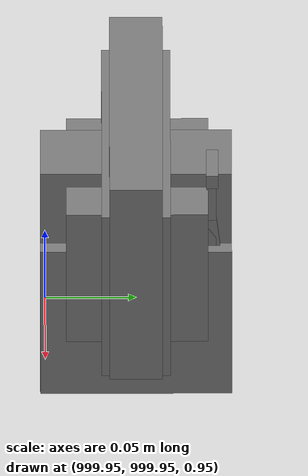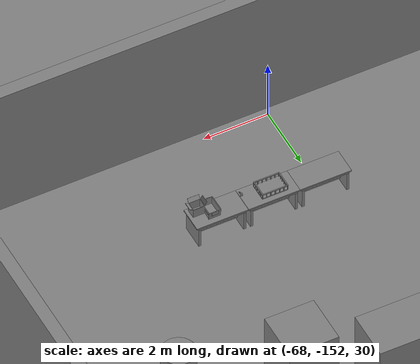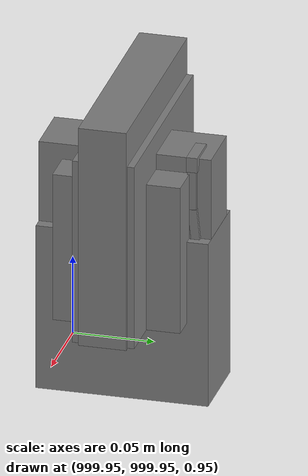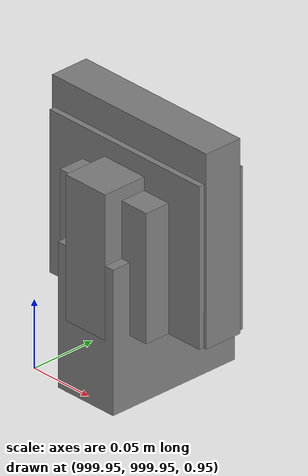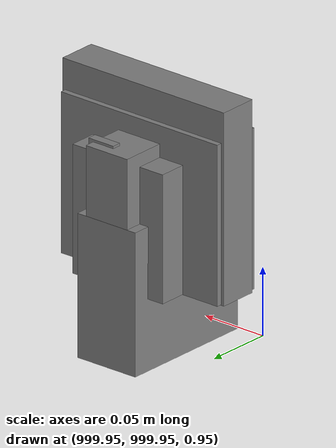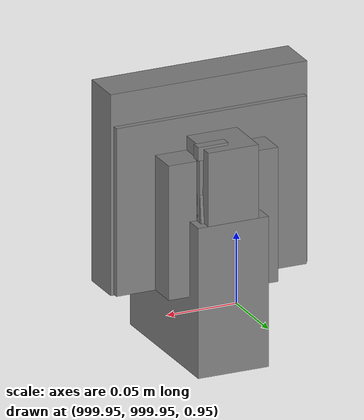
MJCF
<mujoco>
    <option gravity="0.000000000 0.000000000 -9.810000420" timestep="0.0049999999" integrator="implicitfast" density="1.225" viscosity="1.8000001e-05" noslip_iterations="10" iterations="100" sdf_iterations="50">
        <flag multiccd="disable"/>
    </option>
    <size memory="1000M"/>
    <compiler coordinate="local"/>
    <worldbody>
        <light cutoff="30" pos="0 1 1" dir="0 -1 -2"/>
        <light cutoff="30" pos="0 -1 1" dir="0 1 -2"/>
        <body pos="-64.866622925 -149.383972168 30.183746338" euler="89.999984741 89.999946594 0.000000000" name="openloong_gripper_2f85_fix_base_usda_bluebox_01">
            <geom contype="1" conaffinity="1" density="1000" type="box" material="" rgba="0.500000000 0.500000000 0.500000000 1.000000000" solimp="0.899999976 0.949999988 0.001000000" friction="1.000000000 0.005000000 0.000100000" solref="0.020000000 1.000000000" margin="0" condim="3" group="0" pos="0.276580811 0.187225342 0.000068665" quat="0.707106948 0.000077471 0.707106352 0.000077486" size="0.100000001 0.057999998 0.010000000" name="openloong_gripper_2f85_fix_base_usda_geom_0AC14013_EB70_49B1_9C88_F200C88A9102"/>
            <geom contype="1" conaffinity="1" density="1000" type="box" material="" rgba="0.500000000 0.500000000 0.500000000 1.000000000" solimp="0.899999976 0.949999988 0.001000000" friction="1.000000000 0.005000000 0.000100000" solref="0.020000000 1.000000000" margin="0" condim="3" group="0" pos="0.000000000 0.002883911 0.000000000" quat="0.999999881 0.000000000 0.000000000 0.000000000" size="0.254000008 0.003000000 0.172000006" name="openloong_gripper_2f85_fix_base_usda_geom_A352CDAD_EBF1_4E1E_8575_B38CF1F4BEB6"/>
            <geom contype="1" conaffinity="1" density="1000" type="box" material="" rgba="0.500000000 0.500000000 0.500000000 1.000000000" solimp="0.899999976 0.949999988 0.001000000" friction="1.000000000 0.005000000 0.000100000" solref="0.020000000 1.000000000" margin="0" condim="3" group="0" pos="0.000000000 0.124874115 0.173484802" quat="0.999796331 0.020176515 -0.000000015 0.000000030" size="0.259999990 0.119999997 0.007000000" name="openloong_gripper_2f85_fix_base_usda_geom_D4D0316D_0F4F_4D1E_ABE8_2CF4F47D9733"/>
            <geom contype="1" conaffinity="1" density="1000" type="box" material="" rgba="0.500000000 0.500000000 0.500000000 1.000000000" solimp="0.899999976 0.949999988 0.001000000" friction="1.000000000 0.005000000 0.000100000" solref="0.020000000 1.000000000" margin="0" condim="3" group="0" pos="0.000000000 0.124874115 -0.173469543" quat="0.999796331 -0.020176545 -0.000000015 0.000000000" size="0.259999990 0.119999997 0.007000000" name="openloong_gripper_2f85_fix_base_usda_geom_0F208F2A_7495_4B05_A18F_ABA2AA63272B"/>
            <geom contype="1" conaffinity="1" density="1000" type="box" material="" rgba="0.500000000 0.500000000 0.500000000 1.000000000" solimp="0.899999976 0.949999988 0.001000000" friction="1.000000000 0.005000000 0.000100000" solref="0.020000000 1.000000000" margin="0" condim="3" group="0" pos="0.000000000 0.214008331 0.188980103" quat="0.999912977 0.013176724 0.000000015 0.000000000" size="0.259999990 0.029999999 0.012500000" name="openloong_gripper_2f85_fix_base_usda_geom_F4018800_894D_490F_A506_922B50A87109"/>
            <geom contype="1" conaffinity="1" density="1000" type="box" material="" rgba="0.500000000 0.500000000 0.500000000 1.000000000" solimp="0.899999976 0.949999988 0.001000000" friction="1.000000000 0.005000000 0.000100000" solref="0.020000000 1.000000000" margin="0" condim="3" group="0" pos="-0.258361816 0.125289917 0.001876831" quat="0.702796936 -0.020792112 0.710783124 0.020769298" size="0.189999998 0.119999997 0.009000000" name="openloong_gripper_2f85_fix_base_usda_geom_6ECE9408_97AC_41FC_A1B9_7F2171E5E910"/>
            <geom contype="1" conaffinity="1" density="1000" type="box" material="" rgba="0.500000000 0.500000000 0.500000000 1.000000000" solimp="0.899999976 0.949999988 0.001000000" friction="1.000000000 0.005000000 0.000100000" solref="0.020000000 1.000000000" margin="0" condim="3" group="0" pos="0.000000000 0.214008331 -0.188980103" quat="0.999912977 -0.013176769 0.000000030 0.000000015" size="0.259999990 0.029999999 0.012500000" name="openloong_gripper_2f85_fix_base_usda_geom_1CA0B978_1D6A_4EA0_A999_BF23834F641C"/>
            <geom contype="1" conaffinity="1" density="1000" type="box" material="" rgba="0.500000000 0.500000000 0.500000000 1.000000000" solimp="0.899999976 0.949999988 0.001000000" friction="1.000000000 0.005000000 0.000100000" solref="0.020000000 1.000000000" margin="0" condim="3" group="0" pos="-0.276611328 0.187225342 0.000068665" quat="0.707106650 0.000077441 0.707106709 0.000077456" size="0.100000001 0.057999998 0.010000000" name="openloong_gripper_2f85_fix_base_usda_geom_68273B9D_9092_4993_A3E4_3F1B6E5FF3BD"/>
            <geom contype="1" conaffinity="1" density="1000" type="box" material="" rgba="0.500000000 0.500000000 0.500000000 1.000000000" solimp="0.899999976 0.949999988 0.001000000" friction="1.000000000 0.005000000 0.000100000" solref="0.020000000 1.000000000" margin="0" condim="3" group="0" pos="0.258331299 0.125289917 0.001876831" quat="0.702851415 0.018856421 0.710823774 -0.019329369" size="0.189999998 0.119999997 0.009000000" name="openloong_gripper_2f85_fix_base_usda_geom_44BB9164_9FAC_4E17_BE7C_D1E941C07058"/>
            <freejoint name="openloong_gripper_2f85_fix_base_usda_bluebox_01_joint"/>
            <site size="0.005000000 0.005000000 0.005000000" rgba="0.500000000 0.500000000 0.500000000 1.000000000" pos="0.000000000 0.000000000 0.000000000" quat="0.999961913 0.008726534 0.000000000 0.000000000" group="0" type="sphere" name="openloong_gripper_2f85_fix_base_usda_bluebox_01site"/>
        </body>
        <body pos="-64.496299744 -149.491867065 30.235729218" euler="0.000000000 0.000000000 89.999946594" name="openloong_gripper_2f85_fix_base_usda_cardboardbox_01">
            <geom contype="1" conaffinity="1" density="1000" type="box" material="" rgba="0.500000000 0.500000000 0.500000000 1.000000000" solimp="0.899999976 0.949999988 0.001000000" friction="1.000000000 0.005000000 0.000100000" solref="0.020000000 1.000000000" margin="0" condim="3" group="0" pos="-0.003166199 -0.004086494 0.005052090" quat="1.000000000 0.000000000 0.000000000 0.000000000" size="0.142499998 0.177500010 0.005000000" name="openloong_gripper_2f85_fix_base_usda_geom_53F62DC7_9D09_467C_A6BA_44D2DD33871D"/>
            <geom contype="1" conaffinity="1" density="1000" type="box" material="" rgba="0.500000000 0.500000000 0.500000000 1.000000000" solimp="0.899999976 0.949999988 0.001000000" friction="1.000000000 0.005000000 0.000100000" solref="0.020000000 1.000000000" margin="0" condim="3" group="0" pos="-0.003166199 0.170316696 0.150570869" quat="1.000000000 0.000000000 0.000000000 0.000000000" size="0.142499998 0.005000000 0.149999991" name="openloong_gripper_2f85_fix_base_usda_geom_EAF5EED6_6052_4BD2_A79B_0E9C7C590686"/>
            <geom contype="1" conaffinity="1" density="1000" type="box" material="" rgba="0.500000000 0.500000000 0.500000000 1.000000000" solimp="0.899999976 0.949999988 0.001000000" friction="1.000000000 0.005000000 0.000100000" solref="0.020000000 1.000000000" margin="0" condim="3" group="0" pos="-0.147399902 -0.005307198 0.150570869" quat="1.000000000 0.000000000 0.000000000 0.000000000" size="0.005000000 0.177500010 0.149999991" name="openloong_gripper_2f85_fix_base_usda_geom_FA22667F_753B_4CA8_8477_61D7BCE53603"/>
            <geom contype="1" conaffinity="1" density="1000" type="box" material="" rgba="0.500000000 0.500000000 0.500000000 1.000000000" solimp="0.899999976 0.949999988 0.001000000" friction="1.000000000 0.005000000 0.000100000" solref="0.020000000 1.000000000" margin="0" condim="3" group="0" pos="0.140275955 -0.005307198 0.150570869" quat="1.000000000 0.000000000 0.000000000 0.000000000" size="0.005000000 0.177500010 0.149999991" name="openloong_gripper_2f85_fix_base_usda_geom_084D5D21_E6A4_4845_A153_AAA2D6947DCD"/>
            <geom contype="1" conaffinity="1" density="1000" type="box" material="" rgba="0.500000000 0.500000000 0.500000000 1.000000000" solimp="0.899999976 0.949999988 0.001000000" friction="1.000000000 0.005000000 0.000100000" solref="0.020000000 1.000000000" margin="0" condim="3" group="0" pos="-0.003166199 -0.181550980 0.150570869" quat="1.000000000 0.000000000 0.000000000 0.000000000" size="0.142499998 0.005000000 0.149999991" name="openloong_gripper_2f85_fix_base_usda_geom_F5626431_A40C_40B1_8C5F_1CC480D8A25A"/>
            <freejoint name="openloong_gripper_2f85_fix_base_usda_cardboardbox_01_joint"/>
            <site size="0.005000000 0.005000000 0.005000000" rgba="0.500000000 0.500000000 0.500000000 1.000000000" pos="0.000000000 0.000000000 0.000000000" quat="0.999961913 0.008726535 0.000000000 0.000000000" group="0" type="sphere" name="openloong_gripper_2f85_fix_base_usda_site_FD40FAB0_A3C9_4418_A9B8_5A99150DB58F"/>
            <body pos="0.139160156 -0.004048347 0.301930904" euler="-179.999954224 49.383502960 179.999954224" name="openloong_gripper_2f85_fix_base_usda_A1_006">
                <geom contype="1" conaffinity="1" density="1000" type="box" material="" rgba="0.500000000 0.500000000 0.500000000 1.000000000" solimp="0.899999976 0.949999988 0.001000000" friction="1.000000000 0.005000000 0.000100000" solref="0.020000000 1.000000000" margin="0" condim="3" group="0" pos="-0.071587563 0.000009537 0.001745224" quat="0.999999881 0.000000000 0.000000000 0.000000000" size="0.071249999 0.179999992 0.002500000" name="openloong_gripper_2f85_fix_base_usda_geom_A97A6264_1317_478F_96D2_E6099B44AF4C"/>
                <joint armature="0" stiffness="0.07" damping="0.0099999998" axis="0.000000 1.000000 0.000000" type="hinge" name="openloong_gripper_2f85_fix_base_usda_A1_006"/>
            </body>
            <body pos="-0.145902634 -0.004086494 0.301938057" euler="-180.000000000 -60.000011444 -180.000000000" name="openloong_gripper_2f85_fix_base_usda_A2_006">
                <geom contype="1" conaffinity="1" density="1000" type="box" material="" rgba="0.500000000 0.500000000 0.500000000 1.000000000" solimp="0.899999976 0.949999988 0.001000000" friction="1.000000000 0.005000000 0.000100000" solref="0.020000000 1.000000000" margin="0" condim="3" group="0" pos="0.071268082 0.000009537 0.002717972" quat="0.000002921 0.000000000 -0.000000030 0.999999881" size="0.071249999 0.179999992 0.002500000" name="openloong_gripper_2f85_fix_base_usda_geom_19404C95_B7E6_469F_B74D_8BF429CB1074"/>
                <joint armature="0" stiffness="0.07" damping="0.0099999998" axis="0.000000 1.000000 0.000000" type="hinge" name="openloong_gripper_2f85_fix_base_usda_A2_006"/>
            </body>
            <body pos="-0.003385544 0.175991058 0.301930904" euler="-125.858116150 -0.000004561 0.000002331" name="openloong_gripper_2f85_fix_base_usda_B2_006">
                <geom contype="1" conaffinity="1" density="1000" type="box" material="" rgba="0.500000000 0.500000000 0.500000000 1.000000000" solimp="0.899999976 0.949999988 0.001000000" friction="1.000000000 0.005000000 0.000100000" solref="0.020000000 1.000000000" margin="0" condim="3" group="0" pos="0.000009537 -0.070939064 -0.002470016" quat="0.999614120 0.027776197 -0.000000015 0.000000030" size="0.137500003 0.064999998 0.005000000" name="openloong_gripper_2f85_fix_base_usda_geom_9CC04BB7_66DA_4D15_BB1D_5F3421B67CFB"/>
                <joint armature="0" stiffness="0.07" damping="0.0099999998" axis="1.000000 0.000000 0.000000" type="hinge" name="openloong_gripper_2f85_fix_base_usda_B2_006"/>
            </body>
            <body pos="-0.003385544 -0.184140205 0.301938057" euler="147.805557251 0.000000000 0.000000000" name="openloong_gripper_2f85_fix_base_usda_B1_006">
                <geom contype="1" conaffinity="1" density="1000" type="box" material="" rgba="0.500000000 0.500000000 0.500000000 1.000000000" solimp="0.899999976 0.949999988 0.001000000" friction="1.000000000 0.005000000 0.000100000" solref="0.020000000 1.000000000" margin="0" condim="3" group="0" pos="-0.000028610 0.070202351 -0.002703667" quat="0.999614179 -0.027776167 0.000000000 0.000000000" size="0.137500003 0.064999998 0.005000000" name="openloong_gripper_2f85_fix_base_usda_geom_CD883F9A_B98F_4107_9ED4_2C2B45B50F26"/>
                <joint armature="0" stiffness="0.07" damping="0.0099999998" axis="1.000000 0.000000 0.000000" type="hinge" name="openloong_gripper_2f85_fix_base_usda_B1_006"/>
            </body>
        </body>
        <body pos="-65.882858276 -149.481979370 30.229999542" euler="-64.487716675 0.000000000 0.000000000" name="openloong_gripper_2f85_fix_base_usda_Barcode">
            <geom contype="1" conaffinity="1" density="1000" type="box" material="" rgba="0.500000000 0.500000000 0.500000000 1.000000000" solimp="0.899999976 0.949999988 0.001000000" friction="1.000000000 0.005000000 0.000100000" solref="0.020000000 1.000000000" margin="0" condim="3" group="0" pos="0.000000000 0.013038635 0.001419067" quat="0.000000000 0.000000000 0.000000000 1.000000119" size="0.034000002 0.010000000 0.017999999" name="openloong_gripper_2f85_fix_base_usda_geom_F6B87500_E690_49A3_ABD6_53116FCEDC54"/>
            <geom contype="1" conaffinity="1" density="1000" type="box" material="" rgba="0.500000000 0.500000000 0.500000000 1.000000000" solimp="0.899999976 0.949999988 0.001000000" friction="1.000000000 0.005000000 0.000100000" solref="0.020000000 1.000000000" margin="0" condim="3" group="0" pos="0.000000000 -0.035301208 -0.007095337" quat="0.000000000 0.000000000 -0.043619365 0.999048233" size="0.028999999 0.010000000 0.020000000" name="openloong_gripper_2f85_fix_base_usda_geom_9423A033_28BA_49CB_AFD2_F84848CE41AE"/>
            <geom contype="1" conaffinity="1" density="1000" type="box" material="" rgba="0.500000000 0.500000000 0.500000000 1.000000000" solimp="0.899999976 0.949999988 0.001000000" friction="1.000000000 0.005000000 0.000100000" solref="0.020000000 1.000000000" margin="0" condim="3" group="0" pos="0.000000000 -0.043411255 -0.011749268" quat="0.922262907 0.386563420 0.000000000 0.000000000" size="0.026000001 0.010000000 0.020000000" name="openloong_gripper_2f85_fix_base_usda_geom_A7733627_ACB5_46F9_92F6_334FB992B9B9"/>
            <geom contype="1" conaffinity="1" density="1000" type="box" material="" rgba="0.500000000 0.500000000 0.500000000 1.000000000" solimp="0.899999976 0.949999988 0.001000000" friction="1.000000000 0.005000000 0.000100000" solref="0.020000000 1.000000000" margin="0" condim="3" group="0" pos="0.000000000 -0.016967773 -0.031860352" quat="0.000000000 0.000000000 0.000000000 1.000000119" size="0.008000000 0.010000000 0.013000000" name="openloong_gripper_2f85_fix_base_usda_geom_421EDEA0_E6E4_48AC_8D98_6A868EBE0351"/>
            <geom contype="1" conaffinity="1" density="1000" type="box" material="" rgba="0.500000000 0.500000000 0.500000000 1.000000000" solimp="0.899999976 0.949999988 0.001000000" friction="1.000000000 0.005000000 0.000100000" solref="0.020000000 1.000000000" margin="0" condim="3" group="0" pos="0.000000000 -0.001869202 0.000312805" quat="0.953716993 0.300705761 0.000000000 0.000000000" size="0.032000002 0.010000000 0.018999999" name="openloong_gripper_2f85_fix_base_usda_geom_A682FD28_FC01_400E_B02C_37631B3502BC"/>
            <geom contype="1" conaffinity="1" density="1000" type="box" material="" rgba="0.500000000 0.500000000 0.500000000 1.000000000" solimp="0.899999976 0.949999988 0.001000000" friction="1.000000000 0.005000000 0.000100000" solref="0.020000000 1.000000000" margin="0" condim="3" group="0" pos="0.000000000 -0.019531250 -0.003173828" quat="0.953716993 0.300705761 0.000000000 0.000000000" size="0.030999999 0.010000000 0.020000000" name="openloong_gripper_2f85_fix_base_usda_geom_975671E2_3275_4D14_B12B_BBCBE6547B77"/>
            <geom contype="1" conaffinity="1" density="1000" type="box" material="" rgba="0.500000000 0.500000000 0.500000000 1.000000000" solimp="0.899999976 0.949999988 0.001000000" friction="1.000000000 0.005000000 0.000100000" solref="0.020000000 1.000000000" margin="0" condim="3" group="0" pos="0.000000000 -0.035301208 -0.007095337" quat="0.953716993 0.300705761 0.000000000 0.000000000" size="0.028999999 0.010000000 0.020000000" name="openloong_gripper_2f85_fix_base_usda_geom_199F4229_5BE6_4750_8596_A2D9D1111F4D"/>
            <geom contype="1" conaffinity="1" density="1000" type="box" material="" rgba="0.500000000 0.500000000 0.500000000 1.000000000" solimp="0.899999976 0.949999988 0.001000000" friction="1.000000000 0.005000000 0.000100000" solref="0.020000000 1.000000000" margin="0" condim="3" group="0" pos="0.000000000 -0.042617798 -0.071121216" quat="0.000000000 0.000000000 0.000000000 1.000000119" size="0.013000000 0.021000000 0.059999999" name="openloong_gripper_2f85_fix_base_usda_geom_41691089_7A28_43DD_8DC0_12C8F835917D"/>
            <freejoint name="openloong_gripper_2f85_fix_base_usda_Barcode_joint"/>
            <site size="0.005000000 0.005000000 0.005000000" rgba="0.500000000 0.500000000 0.500000000 1.000000000" pos="0.000000000 0.000000000 0.000000000" quat="1.000000000 0.000000000 0.000000000 0.000000000" group="0" type="sphere" name="openloong_gripper_2f85_fix_base_usda_Barcode_site"/>
        </body>
        <body pos="-66.745018005 -149.392349243 30.184000015" euler="0.000000000 0.000000000 89.999946594" name="[22332757065064]_Basket_01">
            <geom contype="1" conaffinity="1" density="1000" type="box" material="" rgba="0.500000000 0.500000000 0.500000000 1.000000000" solimp="0.899999976 0.949999988 0.001000000" friction="1.000000000 0.005000000 0.000100000" solref="0.020000000 1.000000000" margin="0" condim="3" group="0" pos="-0.052425385 0.389207840 0.089787483" quat="0.707107008 0.000000000 0.000000000 0.707106411" size="0.014249999 0.014249999 0.059999999" name="[22332757065064]_geom_81618413_E257_43ED_99AA_B244A2A1E118"/>
            <geom contype="1" conaffinity="1" density="1000" type="box" material="" rgba="0.500000000 0.500000000 0.500000000 1.000000000" solimp="0.899999976 0.949999988 0.001000000" friction="1.000000000 0.005000000 0.000100000" solref="0.020000000 1.000000000" margin="0" condim="3" group="0" pos="0.264015198 -0.133043289 0.089787483" quat="0.707107008 0.000000000 0.000000000 0.707106411" size="0.014249999 0.014249999 0.059999999" name="[22332757065064]_geom_7C0EF4C5_3EA8_4602_A729_0DC2BCEDE97C"/>
            <geom contype="1" conaffinity="1" density="1000" type="box" material="" rgba="0.500000000 0.500000000 0.500000000 1.000000000" solimp="0.899999976 0.949999988 0.001000000" friction="1.000000000 0.005000000 0.000100000" solref="0.020000000 1.000000000" margin="0" condim="3" group="0" pos="-0.264015198 -0.265548706 0.089793205" quat="0.707107008 0.000000000 0.000000000 0.707106411" size="0.014249999 0.014249999 0.059999999" name="[22332757065064]_geom_96ABD0F6_8D54_47CE_A86F_FE990A0ABE9F"/>
            <geom contype="1" conaffinity="1" density="1000" type="box" material="" rgba="0.500000000 0.500000000 0.500000000 1.000000000" solimp="0.899999976 0.949999988 0.001000000" friction="1.000000000 0.005000000 0.000100000" solref="0.020000000 1.000000000" margin="0" condim="3" group="0" pos="-0.160263062 -0.389322281 0.089793205" quat="0.707107008 0.000000000 0.000000000 0.707106411" size="0.014249999 0.014249999 0.059999999" name="[22332757065064]_geom_1509B622_3424_40D2_A8C8_1917B6C50ACB"/>
            <geom contype="1" conaffinity="1" density="1000" type="box" material="" rgba="0.500000000 0.500000000 0.500000000 1.000000000" solimp="0.899999976 0.949999988 0.001000000" friction="1.000000000 0.005000000 0.000100000" solref="0.020000000 1.000000000" margin="0" condim="3" group="0" pos="0.162265778 -0.389322281 0.089787483" quat="0.707107008 0.000000000 0.000000000 0.707106411" size="0.014249999 0.014249999 0.059999999" name="[22332757065064]_geom_E630E9DC_B857_4690_9C91_AC227E77D300"/>
            <geom contype="1" conaffinity="1" density="1000" type="box" material="" rgba="0.500000000 0.500000000 0.500000000 1.000000000" solimp="0.899999976 0.949999988 0.001000000" friction="1.000000000 0.005000000 0.000100000" solref="0.020000000 1.000000000" margin="0" condim="3" group="0" pos="0.264015198 0.389207840 0.089787483" quat="0.707107008 0.000000000 0.000000000 0.707106411" size="0.014249999 0.014249999 0.059999999" name="[22332757065064]_geom_E87CDEBC_5B6A_4CFC_BE22_4CC3543D19B9"/>
            <geom contype="1" conaffinity="1" density="1000" type="box" material="" rgba="0.500000000 0.500000000 0.500000000 1.000000000" solimp="0.899999976 0.949999988 0.001000000" friction="1.000000000 0.005000000 0.000100000" solref="0.020000000 1.000000000" margin="0" condim="3" group="0" pos="-0.264015198 -0.133043289 0.089793205" quat="0.707107008 0.000000000 0.000000000 0.707106411" size="0.014249999 0.014249999 0.059999999" name="[22332757065064]_geom_3BD4C13A_0007_4E88_B339_C15C595F5457"/>
            <geom contype="1" conaffinity="1" density="1000" type="box" material="" rgba="0.500000000 0.500000000 0.500000000 1.000000000" solimp="0.899999976 0.949999988 0.001000000" friction="1.000000000 0.005000000 0.000100000" solref="0.020000000 1.000000000" margin="0" condim="3" group="0" pos="-0.264026642 0.269256592 0.089793205" quat="0.707107008 0.000000000 0.000000000 0.707106411" size="0.014249999 0.014249999 0.059999999" name="[22332757065064]_geom_E431F65E_D103_4F5C_A229_9B194663F536"/>
            <geom contype="1" conaffinity="1" density="1000" type="box" material="" rgba="0.500000000 0.500000000 0.500000000 1.000000000" solimp="0.899999976 0.949999988 0.001000000" friction="1.000000000 0.005000000 0.000100000" solref="0.020000000 1.000000000" margin="0" condim="3" group="0" pos="0.054462433 0.389207840 0.089787483" quat="0.707107008 0.000000000 0.000000000 0.707106411" size="0.014249999 0.014249999 0.059999999" name="[22332757065064]_geom_AE50F8F4_D5F1_4E8F_9285_59431BDDD267"/>
            <geom contype="1" conaffinity="1" density="1000" type="box" material="" rgba="0.500000000 0.500000000 0.500000000 1.000000000" solimp="0.899999976 0.949999988 0.001000000" friction="1.000000000 0.005000000 0.000100000" solref="0.020000000 1.000000000" margin="0" condim="3" group="0" pos="0.054462433 -0.389322281 0.089787483" quat="0.707107008 0.000000000 0.000000000 0.707106411" size="0.014249999 0.014249999 0.059999999" name="[22332757065064]_geom_E0E6FF93_6202_43A6_8BFF_307CB1314505"/>
            <geom contype="1" conaffinity="1" density="1000" type="box" material="" rgba="0.500000000 0.500000000 0.500000000 1.000000000" solimp="0.899999976 0.949999988 0.001000000" friction="1.000000000 0.005000000 0.000100000" solref="0.020000000 1.000000000" margin="0" condim="3" group="0" pos="0.264015198 0.269256592 0.089793205" quat="0.707107008 0.000000000 0.000000000 0.707106411" size="0.014249999 0.014249999 0.059999999" name="[22332757065064]_geom_F0FD0255_7876_41D3_B242_227455854F3E"/>
            <geom contype="1" conaffinity="1" density="1000" type="box" material="" rgba="0.500000000 0.500000000 0.500000000 1.000000000" solimp="0.899999976 0.949999988 0.001000000" friction="1.000000000 0.005000000 0.000100000" solref="0.020000000 1.000000000" margin="0" condim="3" group="0" pos="0.264015198 -0.389322281 0.089787483" quat="0.707107008 0.000000000 0.000000000 0.707106411" size="0.014249999 0.014249999 0.059999999" name="[22332757065064]_geom_9702049A_4452_4275_8A97_032BAFE882BC"/>
            <geom contype="1" conaffinity="1" density="1000" type="box" material="" rgba="0.500000000 0.500000000 0.500000000 1.000000000" solimp="0.899999976 0.949999988 0.001000000" friction="1.000000000 0.005000000 0.000100000" solref="0.020000000 1.000000000" margin="0" condim="3" group="0" pos="0.000000000 0.000000000 0.015998840" quat="0.707107008 0.000000000 0.000000000 0.707106411" size="0.403499991 0.279000014 0.015750000" name="[22332757065064]_geom_9064BB03_87EA_4BBD_8B61_860445FF0217"/>
            <geom contype="1" conaffinity="1" density="1000" type="box" material="" rgba="0.500000000 0.500000000 0.500000000 1.000000000" solimp="0.899999976 0.949999988 0.001000000" friction="1.000000000 0.005000000 0.000100000" solref="0.020000000 1.000000000" margin="0" condim="3" group="0" pos="0.000000000 -0.389476776 0.163619041" quat="0.707107008 0.000000000 0.000000000 0.707106411" size="0.015000000 0.277500004 0.015750000" name="[22332757065064]_geom_6873634A_E6A8_4B7C_96B9_F634FFAAD0CB"/>
            <geom contype="1" conaffinity="1" density="1000" type="box" material="" rgba="0.500000000 0.500000000 0.500000000 1.000000000" solimp="0.899999976 0.949999988 0.001000000" friction="1.000000000 0.005000000 0.000100000" solref="0.020000000 1.000000000" margin="0" condim="3" group="0" pos="0.162265778 0.389207840 0.089787483" quat="0.707107008 0.000000000 0.000000000 0.707106411" size="0.014249999 0.014249999 0.059999999" name="[22332757065064]_geom_3263AAD7_3127_47FF_ADFE_363FA6DC9316"/>
            <geom contype="1" conaffinity="1" density="1000" type="box" material="" rgba="0.500000000 0.500000000 0.500000000 1.000000000" solimp="0.899999976 0.949999988 0.001000000" friction="1.000000000 0.005000000 0.000100000" solref="0.020000000 1.000000000" margin="0" condim="3" group="0" pos="0.000000000 0.389471054 0.163619041" quat="0.707107008 0.000000000 0.000000000 0.707106411" size="0.015000000 0.277500004 0.015750000" name="[22332757065064]_geom_334C6D73_97E7_4A8F_A412_484A71957BA1"/>
            <geom contype="1" conaffinity="1" density="1000" type="box" material="" rgba="0.500000000 0.500000000 0.500000000 1.000000000" solimp="0.899999976 0.949999988 0.001000000" friction="1.000000000 0.005000000 0.000100000" solref="0.020000000 1.000000000" margin="0" condim="3" group="0" pos="-0.263511658 0.000000000 0.163619041" quat="0.707107008 0.000000000 0.000000000 0.707106411" size="0.403499991 0.015000000 0.015750000" name="[22332757065064]_geom_B146AC47_2FF5_4D10_A4B6_20D9B0AA6755"/>
            <geom contype="1" conaffinity="1" density="1000" type="box" material="" rgba="0.500000000 0.500000000 0.500000000 1.000000000" solimp="0.899999976 0.949999988 0.001000000" friction="1.000000000 0.005000000 0.000100000" solref="0.020000000 1.000000000" margin="0" condim="3" group="0" pos="-0.264015198 0.141334534 0.089793205" quat="0.707107008 0.000000000 0.000000000 0.707106411" size="0.014249999 0.014249999 0.059999999" name="[22332757065064]_geom_DF54B15C_4AA7_4D65_9748_651175CFE432"/>
            <geom contype="1" conaffinity="1" density="1000" type="box" material="" rgba="0.500000000 0.500000000 0.500000000 1.000000000" solimp="0.899999976 0.949999988 0.001000000" friction="1.000000000 0.005000000 0.000100000" solref="0.020000000 1.000000000" margin="0" condim="3" group="0" pos="0.264015198 -0.265548706 0.089787483" quat="0.707107008 0.000000000 0.000000000 0.707106411" size="0.014249999 0.014249999 0.059999999" name="[22332757065064]_geom_2F0C85C5_8B97_4E08_9EB5_2C8F77C1A80C"/>
            <geom contype="1" conaffinity="1" density="1000" type="box" material="" rgba="0.500000000 0.500000000 0.500000000 1.000000000" solimp="0.899999976 0.949999988 0.001000000" friction="1.000000000 0.005000000 0.000100000" solref="0.020000000 1.000000000" margin="0" condim="3" group="0" pos="-0.160263062 0.389207840 0.089787483" quat="0.707107008 0.000000000 0.000000000 0.707106411" size="0.014249999 0.014249999 0.059999999" name="[22332757065064]_geom_93A9DE02_F241_4AA9_A951_D656F9AEDA39"/>
            <geom contype="1" conaffinity="1" density="1000" type="box" material="" rgba="0.500000000 0.500000000 0.500000000 1.000000000" solimp="0.899999976 0.949999988 0.001000000" friction="1.000000000 0.005000000 0.000100000" solref="0.020000000 1.000000000" margin="0" condim="3" group="0" pos="-0.052425385 -0.389322281 0.089787483" quat="0.707107008 0.000000000 0.000000000 0.707106411" size="0.014249999 0.014249999 0.059999999" name="[22332757065064]_geom_608B7A91_0BA1_41A6_824B_98E6BA5ED670"/>
            <geom contype="1" conaffinity="1" density="1000" type="box" material="" rgba="0.500000000 0.500000000 0.500000000 1.000000000" solimp="0.899999976 0.949999988 0.001000000" friction="1.000000000 0.005000000 0.000100000" solref="0.020000000 1.000000000" margin="0" condim="3" group="0" pos="-0.264026642 -0.389322281 0.089793205" quat="0.707107008 0.000000000 0.000000000 0.707106411" size="0.014249999 0.014249999 0.059999999" name="[22332757065064]_geom_4DF9FBF4_E13A_4F7A_81DC_0FE3038413C3"/>
            <geom contype="1" conaffinity="1" density="1000" type="box" material="" rgba="0.500000000 0.500000000 0.500000000 1.000000000" solimp="0.899999976 0.949999988 0.001000000" friction="1.000000000 0.005000000 0.000100000" solref="0.020000000 1.000000000" margin="0" condim="3" group="0" pos="0.264015198 0.141334534 0.089787483" quat="0.707107008 0.000000000 0.000000000 0.707106411" size="0.014249999 0.014249999 0.059999999" name="[22332757065064]_geom_E296B667_67B4_4B68_9D63_56156974D9CA"/>
            <geom contype="1" conaffinity="1" density="1000" type="box" material="" rgba="0.500000000 0.500000000 0.500000000 1.000000000" solimp="0.899999976 0.949999988 0.001000000" friction="1.000000000 0.005000000 0.000100000" solref="0.020000000 1.000000000" margin="0" condim="3" group="0" pos="-0.264015198 0.389207840 0.089793205" quat="0.707107008 0.000000000 0.000000000 0.707106411" size="0.014249999 0.014249999 0.059999999" name="[22332757065064]_geom_9D4DAFF3_62C6_464D_A6CA_5D5F4F835919"/>
            <geom contype="1" conaffinity="1" density="1000" type="box" material="" rgba="0.500000000 0.500000000 0.500000000 1.000000000" solimp="0.899999976 0.949999988 0.001000000" friction="1.000000000 0.005000000 0.000100000" solref="0.020000000 1.000000000" margin="0" condim="3" group="0" pos="0.264015198 0.004480362 0.089787483" quat="0.707107008 0.000000000 0.000000000 0.707106411" size="0.014249999 0.014249999 0.059999999" name="[22332757065064]_geom_AFD42A49_23FC_4E56_844D_DC69F5A823CD"/>
            <geom contype="1" conaffinity="1" density="1000" type="box" material="" rgba="0.500000000 0.500000000 0.500000000 1.000000000" solimp="0.899999976 0.949999988 0.001000000" friction="1.000000000 0.005000000 0.000100000" solref="0.020000000 1.000000000" margin="0" condim="3" group="0" pos="0.263694763 -0.000011444 0.163619041" quat="0.707107008 0.000000000 0.000000000 0.707106411" size="0.403499991 0.015000000 0.015750000" name="[22332757065064]_geom_6BDD0259_84F1_49F0_8BCC_9E9EF0C94D2D"/>
            <geom contype="1" conaffinity="1" density="1000" type="box" material="" rgba="0.500000000 0.500000000 0.500000000 1.000000000" solimp="0.899999976 0.949999988 0.001000000" friction="1.000000000 0.005000000 0.000100000" solref="0.020000000 1.000000000" margin="0" condim="3" group="0" pos="-0.264015198 0.004480362 0.089793205" quat="0.707107008 0.000000000 0.000000000 0.707106411" size="0.014249999 0.014249999 0.059999999" name="[22332757065064]_geom_61EF3D2F_30E0_426E_B6C0_5CB71881C828"/>
            <freejoint name="[22332757065064]_joint_BF9891EC_FC74_4797_AC34_AB4B2BCD6348"/>
        </body>
        <body pos="0.000000000 0.000000000 0.000000000" euler="0.000000000 0.000000000 0.000000000" name="Static Objects_Static Objects">
            <geom contype="1" conaffinity="1" density="1000" type="box" material="" rgba="0.500000000 0.500000000 0.500000000 1.000000000" solimp="0.899999976 0.949999988 0.001000000" friction="1.000000000 0.005000000 0.000100000" solref="0.020000000 1.000000000" margin="0" condim="3" group="0" pos="-67.544113159 -149.365814209 29.727830887" quat="0.500000417 0.499999970 0.499999553 0.499999970" size="0.381000012 0.319999993 0.041000001" name="Static Objects_geom_7498FE4B_5117_4A2F_B9E0_1469358CEFED"/>
            <geom contype="1" conaffinity="1" density="1000" type="box" material="" rgba="0.500000000 0.500000000 0.500000000 1.000000000" solimp="0.899999976 0.949999988 0.001000000" friction="1.000000000 0.005000000 0.000100000" solref="0.020000000 1.000000000" margin="0" condim="3" group="0" pos="-68.239501953 -149.365814209 30.086868286" quat="0.500000417 0.499999970 0.499999553 0.499999970" size="0.370999992 0.039500002 0.745000005" name="Static Objects_geom_154A07F6_B736_4E6C_97D8_485DF368CBD2"/>
            <geom contype="1" conaffinity="1" density="1000" type="box" material="" rgba="0.500000000 0.500000000 0.500000000 1.000000000" solimp="0.899999976 0.949999988 0.001000000" friction="1.000000000 0.005000000 0.000100000" solref="0.020000000 1.000000000" margin="0" condim="3" group="0" pos="-68.239501953 -149.365814209 30.147235870" quat="0.500000417 0.499999970 0.499999553 0.499999970" size="0.400000006 0.022000000 0.800000012" name="Static Objects_geom_B4230BDA_3BFC_40B8_A832_D35C7B657CE6"/>
            <geom contype="1" conaffinity="1" density="1000" type="box" material="" rgba="0.500000000 0.500000000 0.500000000 1.000000000" solimp="0.899999976 0.949999988 0.001000000" friction="1.000000000 0.005000000 0.000100000" solref="0.020000000 1.000000000" margin="0" condim="3" group="0" pos="-68.934890747 -149.365814209 29.727830887" quat="0.500000417 0.499999970 0.499999553 0.499999970" size="0.381000012 0.319999993 0.041000001" name="Static Objects_geom_A9276719_F158_4ED9_8802_32B15C69EE5A"/>
            <geom contype="1" conaffinity="1" density="1000" type="box" material="" rgba="0.500000000 0.500000000 0.500000000 1.000000000" solimp="0.899999976 0.949999988 0.001000000" friction="1.000000000 0.005000000 0.000100000" solref="0.020000000 1.000000000" margin="0" condim="3" group="0" pos="-68.239501953 -149.365814209 29.561563492" quat="0.500000417 0.499999970 0.499999553 0.499999970" size="0.020000000 0.022000000 0.660000026" name="Static Objects_geom_98DE6F47_9E99_4C2F_B9BA_A519B0B53E0E"/>
            <geom contype="1" conaffinity="1" density="1000" type="box" material="" rgba="0.500000000 0.500000000 0.500000000 1.000000000" solimp="0.899999976 0.949999988 0.001000000" friction="1.000000000 0.005000000 0.000100000" solref="0.020000000 1.000000000" margin="0" condim="3" group="0" pos="-65.945671082 -149.365814209 29.727830887" quat="0.500000417 0.499999970 0.499999553 0.499999970" size="0.381000012 0.319999993 0.041000001" name="Static Objects_geom_0F4E3FEF_5FA2_4990_A19D_7559564DB3C4"/>
            <geom contype="1" conaffinity="1" density="1000" type="box" material="" rgba="0.500000000 0.500000000 0.500000000 1.000000000" solimp="0.899999976 0.949999988 0.001000000" friction="1.000000000 0.005000000 0.000100000" solref="0.020000000 1.000000000" margin="0" condim="3" group="0" pos="-66.641059875 -149.365814209 30.086868286" quat="0.500000417 0.499999970 0.499999553 0.499999970" size="0.370999992 0.039500002 0.745000005" name="Static Objects_geom_5C1DCF73_518E_461F_AA6D_E645EAF523CD"/>
            <geom contype="1" conaffinity="1" density="1000" type="box" material="" rgba="0.500000000 0.500000000 0.500000000 1.000000000" solimp="0.899999976 0.949999988 0.001000000" friction="1.000000000 0.005000000 0.000100000" solref="0.020000000 1.000000000" margin="0" condim="3" group="0" pos="-66.641059875 -149.365814209 30.147235870" quat="0.500000417 0.499999970 0.499999553 0.499999970" size="0.400000006 0.022000000 0.800000012" name="Static Objects_geom_B483D255_0775_4EE9_B672_9D7B617AFDD9"/>
            <geom contype="1" conaffinity="1" density="1000" type="box" material="" rgba="0.500000000 0.500000000 0.500000000 1.000000000" solimp="0.899999976 0.949999988 0.001000000" friction="1.000000000 0.005000000 0.000100000" solref="0.020000000 1.000000000" margin="0" condim="3" group="0" pos="-67.336448669 -149.365814209 29.727830887" quat="0.500000417 0.499999970 0.499999553 0.499999970" size="0.381000012 0.319999993 0.041000001" name="Static Objects_geom_D21BD57E_8453_40B9_B0BE_E28DFCA2FCB5"/>
            <geom contype="1" conaffinity="1" density="1000" type="box" material="" rgba="0.500000000 0.500000000 0.500000000 1.000000000" solimp="0.899999976 0.949999988 0.001000000" friction="1.000000000 0.005000000 0.000100000" solref="0.020000000 1.000000000" margin="0" condim="3" group="0" pos="-66.641059875 -149.365814209 29.561563492" quat="0.500000417 0.499999970 0.499999553 0.499999970" size="0.020000000 0.022000000 0.660000026" name="Static Objects_geom_917C4D0A_7FAD_4A3F_A54F_5B1D300DB774"/>
            <geom contype="1" conaffinity="1" density="1000" type="box" material="" rgba="0.500000000 0.500000000 0.500000000 1.000000000" solimp="0.899999976 0.949999988 0.001000000" friction="1.000000000 0.005000000 0.000100000" solref="0.020000000 1.000000000" margin="0" condim="3" group="0" pos="-64.338577271 -149.365814209 29.727830887" quat="0.500000417 0.499999970 0.499999553 0.499999970" size="0.381000012 0.319999993 0.041000001" name="Static Objects_geom_82222AB1_CE61_4F21_BB19_7972D9862B40"/>
            <geom contype="1" conaffinity="1" density="1000" type="box" material="" rgba="0.500000000 0.500000000 0.500000000 1.000000000" solimp="0.899999976 0.949999988 0.001000000" friction="1.000000000 0.005000000 0.000100000" solref="0.020000000 1.000000000" margin="0" condim="3" group="0" pos="-65.033966064 -149.365814209 30.086868286" quat="0.500000417 0.499999970 0.499999553 0.499999970" size="0.370999992 0.039500002 0.745000005" name="Static Objects_geom_086B01D9_A4D1_4719_831D_A452A97B8155"/>
            <geom contype="1" conaffinity="1" density="1000" type="box" material="" rgba="0.500000000 0.500000000 0.500000000 1.000000000" solimp="0.899999976 0.949999988 0.001000000" friction="1.000000000 0.005000000 0.000100000" solref="0.020000000 1.000000000" margin="0" condim="3" group="0" pos="-65.033966064 -149.365814209 30.147235870" quat="0.500000417 0.499999970 0.499999553 0.499999970" size="0.400000006 0.022000000 0.800000012" name="Static Objects_geom_4A16B7BB_C959_4156_BD00_B5931DC98D1A"/>
            <geom contype="1" conaffinity="1" density="1000" type="box" material="" rgba="0.500000000 0.500000000 0.500000000 1.000000000" solimp="0.899999976 0.949999988 0.001000000" friction="1.000000000 0.005000000 0.000100000" solref="0.020000000 1.000000000" margin="0" condim="3" group="0" pos="-65.729354858 -149.365814209 29.727830887" quat="0.500000417 0.499999970 0.499999553 0.499999970" size="0.381000012 0.319999993 0.041000001" name="Static Objects_geom_0944A7FE_57B5_4AFB_8DBD_4BCADBDB40A4"/>
            <geom contype="1" conaffinity="1" density="1000" type="box" material="" rgba="0.500000000 0.500000000 0.500000000 1.000000000" solimp="0.899999976 0.949999988 0.001000000" friction="1.000000000 0.005000000 0.000100000" solref="0.020000000 1.000000000" margin="0" condim="3" group="0" pos="-65.033966064 -149.365814209 29.561563492" quat="0.500000417 0.499999970 0.499999553 0.499999970" size="0.020000000 0.022000000 0.660000026" name="Static Objects_geom_4B22266A_13EA_4E20_ACFD_B3D2D0459C27"/>
            <geom contype="1" conaffinity="1" density="1000" type="box" material="" rgba="0.500000000 0.500000000 0.500000000 1.000000000" solimp="0.899999976 0.949999988 0.001000000" friction="1.000000000 0.005000000 0.000100000" solref="0.020000000 1.000000000" margin="0" condim="3" group="0" pos="-61.754566193 -137.853729248 33.906845093" quat="0.707107067 0.000000000 0.000000000 0.707106471" size="0.759999990 0.759999990 4.500000000" name="Static Objects_geom_12C3DCB6_AA70_400A_BCBB_5C7BE29A7FA1"/>
            <geom contype="1" conaffinity="1" density="1000" type="box" material="" rgba="0.500000000 0.500000000 0.500000000 1.000000000" solimp="0.899999976 0.949999988 0.001000000" friction="1.000000000 0.005000000 0.000100000" solref="0.020000000 1.000000000" margin="0" condim="3" group="0" pos="-57.511135101 -144.927108765 31.707921982" quat="1.000000000 0.000000000 0.000000000 0.000000000" size="0.200000003 8.000000000 2.299999952" name="Static Objects_geom_8F0D6A7C_06D9_4559_BE54_56987C8852F3"/>
            <geom contype="1" conaffinity="1" density="1000" type="box" material="" rgba="0.500000000 0.500000000 0.500000000 1.000000000" solimp="0.899999976 0.949999988 0.001000000" friction="1.000000000 0.005000000 0.000100000" solref="0.020000000 1.000000000" margin="0" condim="3" group="0" pos="-80.517646790 -157.574050903 31.688196182" quat="0.707107067 0.000000000 0.000000000 0.707106471" size="0.600000024 0.600000024 2.299999952" name="Static Objects_geom_DBBAAB99_BDC7_46F0_8797_93522C27F7C5"/>
            <geom contype="1" conaffinity="1" density="1000" type="box" material="" rgba="0.500000000 0.500000000 0.500000000 1.000000000" solimp="0.899999976 0.949999988 0.001000000" friction="1.000000000 0.005000000 0.000100000" solref="0.020000000 1.000000000" margin="0" condim="3" group="0" pos="-80.711044312 -147.414932251 31.666158676" quat="1.000000000 0.000000000 0.000000000 0.000000000" size="0.200000003 10.000000000 2.299999952" name="Static Objects_geom_A606425F_973C_4139_9B85_EEA9156849D7"/>
            <geom contype="1" conaffinity="1" density="1000" type="box" material="" rgba="0.500000000 0.500000000 0.500000000 1.000000000" solimp="0.899999976 0.949999988 0.001000000" friction="1.000000000 0.005000000 0.000100000" solref="0.020000000 1.000000000" margin="0" condim="3" group="0" pos="-57.687217712 -137.434692383 31.688196182" quat="0.707107067 0.000000000 0.000000000 0.707106471" size="0.600000024 0.600000024 2.299999952" name="Static Objects_geom_381F1ECE_A4A9_44D4_9906_39D070B09686"/>
            <geom contype="1" conaffinity="1" density="1000" type="box" material="" rgba="0.500000000 0.500000000 0.500000000 1.000000000" solimp="0.899999976 0.949999988 0.001000000" friction="1.000000000 0.005000000 0.000100000" solref="0.020000000 1.000000000" margin="0" condim="3" group="0" pos="-69.537033081 -140.263229370 31.714921951" quat="0.707107067 0.000000000 0.000000000 0.707106471" size="0.759999990 4.500000000 2.299999952" name="Static Objects_geom_67099F93_D61A_43C8_9F04_8CDD39283CE5"/>
            <geom contype="1" conaffinity="1" density="1000" type="box" material="" rgba="0.500000000 0.500000000 0.500000000 1.000000000" solimp="0.899999976 0.949999988 0.001000000" friction="1.000000000 0.005000000 0.000100000" solref="0.020000000 1.000000000" margin="0" condim="3" group="0" pos="-80.073638916 -137.853713989 33.906845093" quat="0.707107067 0.000000000 0.000000000 0.707106471" size="0.759999990 0.759999990 4.500000000" name="Static Objects_geom_6F915A66_8613_4DA0_B7E9_4714D7D3A306"/>
            <geom contype="1" conaffinity="1" density="1000" type="box" material="" rgba="0.500000000 0.500000000 0.500000000 1.000000000" solimp="0.899999976 0.949999988 0.001000000" friction="1.000000000 0.005000000 0.000100000" solref="0.020000000 1.000000000" margin="0" condim="3" group="0" pos="-73.406707764 -155.734664917 31.707921982" quat="1.000000000 0.000000000 0.000000000 0.000000000" size="0.200000003 3.000000000 2.299999952" name="Static Objects_geom_29418EB1_15CD_4B81_A89F_47E77DA4716B"/>
            <geom contype="1" conaffinity="1" density="1000" type="box" material="" rgba="0.500000000 0.500000000 0.500000000 1.000000000" solimp="0.899999976 0.949999988 0.001000000" friction="1.000000000 0.005000000 0.000100000" solref="0.020000000 1.000000000" margin="0" condim="3" group="0" pos="-68.497543335 -137.448257446 31.707921982" quat="0.707107067 0.000000000 0.000000000 0.707106471" size="0.200000003 14.000000000 2.299999952" name="Static Objects_geom_421C9AC5_E589_4162_B343_60744DE4D132"/>
            <geom contype="1" conaffinity="1" density="1000" type="cylinder" material="" rgba="0.500000000 0.500000000 0.500000000 1.000000000" solimp="0.899999976 0.949999988 0.001000000" friction="1.000000000 0.005000000 0.000100000" solref="0.020000000 1.000000000" margin="0" condim="3" group="0" pos="-68.868522644 -142.134506226 31.711090088" quat="0.707107067 0.000000000 0.000000000 0.707106471" size="0.509999990 2.299999952 1.000000000" name="Static Objects_geom_20983AE3_5C8E_47B8_9890_49928EA3816F"/>
            <geom contype="1" conaffinity="1" density="1000" type="plane" material="" rgba="0.500000000 0.500000000 0.500000000 1.000000000" solimp="0.899999976 0.949999988 0.001000000" friction="1.000000000 0.005000000 0.000100000" solref="0.020000000 1.000000000" margin="0" condim="3" group="0" pos="-72.873703003 -147.131927490 29.409669876" quat="1.000000000 0.000000000 0.000000000 0.000000000" size="18.000000000 14.000000000 1.000000000" name="Static Objects_geom_5130CEEC_9447_4EAC_85E6_65B6B7210B20"/>
            <geom contype="1" conaffinity="1" density="1000" type="box" material="" rgba="0.500000000 0.500000000 0.500000000 1.000000000" solimp="0.899999976 0.949999988 0.001000000" friction="1.000000000 0.005000000 0.000100000" solref="0.020000000 1.000000000" margin="0" condim="3" group="0" pos="-79.943580627 -157.782272339 31.707921982" quat="0.707107067 0.000000000 0.000000000 0.707106471" size="0.200000003 7.000000000 2.299999952" name="Static Objects_geom_AEC4449C_B815_4119_BD8C_FF58993B546A"/>
            <geom contype="1" conaffinity="1" density="1000" type="box" material="" rgba="0.500000000 0.500000000 0.500000000 1.000000000" solimp="0.899999976 0.949999988 0.001000000" friction="1.000000000 0.005000000 0.000100000" solref="0.020000000 1.000000000" margin="0" condim="3" group="0" pos="-65.421028137 -152.903442383 31.707921982" quat="0.707107067 0.000000000 0.000000000 0.707106471" size="0.200000003 7.800000191 2.299999952" name="Static Objects_geom_B5ED6BF1_42F1_4A9B_B8B4_A8074CDB3D24"/>
            <geom contype="1" conaffinity="1" density="1000" type="box" material="" rgba="0.500000000 0.500000000 0.500000000 1.000000000" solimp="0.899999976 0.949999988 0.001000000" friction="1.000000000 0.005000000 0.000100000" solref="0.020000000 1.000000000" margin="0" condim="3" group="0" pos="-74.776908875 -149.964416504 31.688196182" quat="1.000000000 0.000000000 0.000000000 0.000000000" size="0.600000024 0.409999996 2.299999952" name="Static Objects_geom_0743F4B2_8D48_4DC4_B19D_6596EC02FDA5"/>
            <geom contype="1" conaffinity="1" density="1000" type="cylinder" material="" rgba="0.500000000 0.500000000 0.500000000 1.000000000" solimp="0.899999976 0.949999988 0.001000000" friction="1.000000000 0.005000000 0.000100000" solref="0.020000000 1.000000000" margin="0" condim="3" group="0" pos="-60.161884308 -142.134506226 31.711090088" quat="0.707107067 0.000000000 0.000000000 0.707106471" size="0.509999990 2.299999952 1.000000000" name="Static Objects_geom_864617F1_1EFB_4BE6_A63F_39F1B939F856"/>
            <geom contype="1" conaffinity="1" density="1000" type="cylinder" material="" rgba="0.500000000 0.500000000 0.500000000 1.000000000" solimp="0.899999976 0.949999988 0.001000000" friction="1.000000000 0.005000000 0.000100000" solref="0.020000000 1.000000000" margin="0" condim="3" group="0" pos="-75.382453918 -149.963455200 31.711090088" quat="0.707107067 0.000000000 0.000000000 0.707106471" size="0.409999996 2.299999952 1.000000000" name="Static Objects_geom_74EB9E03_4538_4674_9A9B_913E77582E47"/>
            <geom contype="1" conaffinity="1" density="1000" type="cylinder" material="" rgba="0.500000000 0.500000000 0.500000000 1.000000000" solimp="0.899999976 0.949999988 0.001000000" friction="1.000000000 0.005000000 0.000100000" solref="0.020000000 1.000000000" margin="0" condim="3" group="0" pos="-74.154960632 -149.963455200 31.711090088" quat="0.707107067 0.000000000 0.000000000 0.707106471" size="0.409999996 2.299999952 1.000000000" name="Static Objects_geom_FD05E55C_0329_4695_A2FC_A6D190D4BD46"/>
            <geom contype="1" conaffinity="1" density="1000" type="cylinder" material="" rgba="0.500000000 0.500000000 0.500000000 1.000000000" solimp="0.899999976 0.949999988 0.001000000" friction="1.000000000 0.005000000 0.000100000" solref="0.020000000 1.000000000" margin="0" condim="3" group="0" pos="-77.566612244 -142.134506226 31.711090088" quat="0.707107067 0.000000000 0.000000000 0.707106471" size="0.509999990 2.299999952 1.000000000" name="Static Objects_geom_B749294F_8579_466E_84D2_D415DF1B0B55"/>
        </body>
        <body pos="1000.000000000 1000.000000000 1.000000000" euler="0.000000000 0.000000000 180.000000000" name="openloong_gripper_2f85_fix_base_usda_cpu_fan">
            <geom contype="1" conaffinity="1" density="1000" type="box" material="" rgba="0.500000000 0.500000000 0.500000000 1.000000000" solimp="0.899999976 0.949999988 0.001000000" friction="1.000000000 0.005000000 0.000100000" solref="0.020000000 1.000000000" margin="0" condim="3" group="0" pos="0.000000000 0.000000000 0.070034981" quat="0.000000000 0.000000000 0.000000000 1.000000000" size="0.070700005 0.014699999 0.070700005" name="openloong_gripper_2f85_fix_base_usda_geom_0E731435_5F29_4C8A_A489_96065EA9ED6B"/>
            <freejoint name="openloong_gripper_2f85_fix_base_usda_cpu_fan_joint"/>
            <site size="0.005000000 0.005000000 0.005000000" rgba="0.500000000 0.500000000 0.500000000 1.000000000" pos="0.000000000 0.000000000 0.000000000" quat="0.999961913 0.008726535 0.000000000 0.000000000" group="0" type="sphere" name="openloong_gripper_2f85_fix_base_usda_cpu_fancsite"/>
        </body>
        <body pos="-65.862258911 -149.644073486 31.162300110" euler="-73.133445740 -60.680912018 165.700576782" mocap="true" name="spotlight6_SpotLight"/>
        <body pos="1000.000000000 1000.000000000 1.000000000" euler="0.000000000 0.000000000 180.000000000" name="openloong_gripper_2f85_fix_base_usda_wifi_box">
            <geom contype="1" conaffinity="1" density="1000" type="box" material="" rgba="0.500000000 0.500000000 0.500000000 1.000000000" solimp="0.899999976 0.949999988 0.001000000" friction="1.000000000 0.005000000 0.000100000" solref="0.020000000 1.000000000" margin="0" condim="3" group="0" pos="0.000000000 0.000000000 0.058978677" quat="0.000000000 0.000000047 0.000000000 1.000000000" size="0.068499997 0.018999999 0.059000000" name="openloong_gripper_2f85_fix_base_usda_geom_02B5091E_7C01_4B19_B8D4_9872A6916BBB"/>
            <freejoint name="openloong_gripper_2f85_fix_base_usda_wifi_box_joint"/>
            <site size="0.005000000 0.005000000 0.005000000" rgba="0.500000000 0.500000000 0.500000000 1.000000000" pos="0.000000000 0.000000000 0.000000000" quat="0.999961913 0.008726500 0.000000000 0.000000000" group="0" type="sphere" name="openloong_gripper_2f85_fix_base_usda_wifi_boxsite"/>
        </body>
        <body pos="1000.000000000 1000.000000000 1.000000000" euler="0.000011953 0.000005123 -179.999984741" name="openloong_gripper_2f85_fix_base_usda_intel_box">
            <geom contype="1" conaffinity="1" density="1000" type="box" material="" rgba="0.500000000 0.500000000 0.500000000 1.000000000" solimp="0.899999976 0.949999988 0.001000000" friction="1.000000000 0.005000000 0.000100000" solref="0.020000000 1.000000000" margin="0" condim="3" group="0" pos="0.000000000 -0.000067139 0.000082284" quat="0.707106709 0.000000225 0.000000253 0.707106650" size="0.052800003 0.025300000 0.052800003" name="openloong_gripper_2f85_fix_base_usda_geom_0D94940E_FE16_4DBF_A519_F5E806B3C8DF"/>
            <freejoint name="openloong_gripper_2f85_fix_base_usda_intel_box_joint"/>
            <site size="0.005000000 0.005000000 0.005000000" rgba="0.500000000 0.500000000 0.500000000 1.000000000" pos="0.000000000 0.000000000 0.000000000" quat="0.999961913 0.008726500 0.000000000 0.000000000" group="0" type="sphere" name="openloong_gripper_2f85_fix_base_usda_intel_boxsite"/>
        </body>
        <body pos="-66.115303040 -149.156494141 31.162248611" euler="-26.751905441 81.878921509 153.963180542" mocap="true" name="spotlight5_SpotLight"/>
        <body pos="1000.000000000 999.999938965 1.000000000" euler="0.000000000 0.000000000 180.000000000" name="openloong_gripper_2f85_fix_base_usda_intelcore_i5">
            <geom contype="1" conaffinity="1" density="1000" type="box" material="" rgba="0.500000000 0.500000000 0.500000000 1.000000000" solimp="0.899999976 0.949999988 0.001000000" friction="1.000000000 0.005000000 0.000100000" solref="0.020000000 1.000000000" margin="0" condim="3" group="0" pos="0.000000000 0.000000000 0.051722717" quat="0.707106709 0.000000000 0.000000000 -0.707106769" size="0.052800000 0.018080002 0.052800000" name="openloong_gripper_2f85_fix_base_usda_geom_7F224414_46A0_40F2_B2B2_DFAF9F8CE14B"/>
            <freejoint name="openloong_gripper_2f85_fix_base_usda_intelcore_i5_joint"/>
            <site size="0.005000000 0.005000000 0.005000000" rgba="0.500000000 0.500000000 0.500000000 1.000000000" pos="0.000000000 0.000000000 0.000000000" quat="0.999961913 0.008726534 0.000000000 0.000000000" group="0" type="sphere" name="openloong_gripper_2f85_fix_base_usda_intelcore_i5site"/>
        </body>
        <body pos="1000.000000000 1000.000000000 1.000000000" euler="0.000000000 0.000000000 180.000000000" name="openloong_gripper_2f85_fix_base_usda_battery_01">
            <geom contype="1" conaffinity="1" density="1000" type="box" material="" rgba="0.500000000 0.500000000 0.500000000 1.000000000" solimp="0.899999976 0.949999988 0.001000000" friction="1.000000000 0.005000000 0.000100000" solref="0.020000000 1.000000000" margin="0" condim="3" group="0" pos="-0.011123657 -0.041940309 0.101691343" quat="1.000000000 0.000000000 0.000000000 0.000000000" size="0.010800000 0.003375000 0.004725000" name="openloong_gripper_2f85_fix_base_usda_geom_0A1AE324_4FF4_45E6_A90F_FC9AD59AF1BF"/>
            <geom contype="1" conaffinity="1" density="1000" type="box" material="" rgba="0.500000000 0.500000000 0.500000000 1.000000000" solimp="0.899999976 0.949999988 0.001000000" friction="1.000000000 0.005000000 0.000100000" solref="0.020000000 1.000000000" margin="0" condim="3" group="0" pos="-0.010876465 -0.044247437 0.047066893" quat="0.998702705 -0.050920475 0.000000000 0.000000000" size="0.009450001 0.002700000 0.024975000" name="openloong_gripper_2f85_fix_base_usda_geom_AC48C923_6886_428B_873C_8B1DAFC863DA"/>
            <geom contype="1" conaffinity="1" density="1000" type="box" material="" rgba="0.500000000 0.500000000 0.500000000 1.000000000" solimp="0.899999976 0.949999988 0.001000000" friction="1.000000000 0.005000000 0.000100000" solref="0.020000000 1.000000000" margin="0" condim="3" group="0" pos="-0.001235962 -0.000659180 0.047381196" quat="1.000000000 0.000000000 0.000000000 0.000000000" size="0.039420001 0.039150000 0.047250003" name="openloong_gripper_2f85_fix_base_usda_geom_959AD419_62EC_4C81_86CB_DEDB21BD4834"/>
            <geom contype="1" conaffinity="1" density="1000" type="box" material="" rgba="0.500000000 0.500000000 0.500000000 1.000000000" solimp="0.899999976 0.949999988 0.001000000" friction="1.000000000 0.005000000 0.000100000" solref="0.020000000 1.000000000" margin="0" condim="3" group="0" pos="-0.010876465 -0.039138794 0.009851727" quat="1.000000000 0.000000000 0.000000000 0.000000000" size="0.009450001 0.010800000 0.013500000" name="openloong_gripper_2f85_fix_base_usda_geom_F1BF8959_4F2A_4BFE_BBBF_0E7BF1D939EB"/>
            <geom contype="1" conaffinity="1" density="1000" type="box" material="" rgba="0.500000000 0.500000000 0.500000000 1.000000000" solimp="0.899999976 0.949999988 0.001000000" friction="1.000000000 0.005000000 0.000100000" solref="0.020000000 1.000000000" margin="0" condim="3" group="0" pos="-0.010876465 -0.041528322 0.071508206" quat="1.000000000 0.000000000 0.000000000 0.000000000" size="0.009450001 0.002700000 0.027000001" name="openloong_gripper_2f85_fix_base_usda_geom_0B771CCF_5052_46A7_A098_579B3C74AF98"/>
            <freejoint name="openloong_gripper_2f85_fix_base_usda_battery_01_joint"/>
            <site size="0.005000000 0.005000000 0.005000000" rgba="0.500000000 0.500000000 0.500000000 1.000000000" pos="0.000000000 0.000000000 0.000000000" quat="0.999961913 0.008726500 0.000000000 0.000000000" group="0" type="sphere" name="openloong_gripper_2f85_fix_base_usda_battery_01site"/>
        </body>
        <body pos="-66.352737427 -148.838577271 31.166929245" euler="-50.742763519 30.854948044 90.394355774" mocap="true" name="spotlight4_SpotLight"/>
        <body pos="-66.291030884 -149.869689941 29.018842697" euler="0.000000000 0.000000000 89.999946594" mocap="true" name="openloong_gripper_2f85_fix_base_usda_leftHandMocap"/>
        <body pos="-66.291030884 -149.869689941 29.018842697" euler="0.000000000 0.000000000 89.999946594" mocap="true" name="openloong_gripper_2f85_fix_base_usda_rightHandMocap"/>
        <body pos="-66.291030884 -149.869689941 30.218843460" euler="0.000000000 0.000000000 89.999946594" name="openloong_gripper_2f85_fix_base_usda_base_link">
            <geom contype="1" conaffinity="1" density="1000" type="mesh" material="" rgba="0.783999979 0.783999979 0.783999979 1.000000000" solimp="0.899999976 0.949999988 0.001000000" friction="1.000000000 0.005000000 0.000100000" solref="0.020000000 1.000000000" margin="0" condim="3" group="3" mesh="base_link" pos="0.000000000 0.000000000 0.000000000" quat="1.000000000 0.000000000 0.000000000 0.000000000" size="1.000000000 1.000000000 1.000000000" name="openloong_gripper_2f85_fix_base_usda__geom_7_C1E6AE86_DBF1_4200_A37F_3278F2FF9CB9"/>
            <site size="0.005000000 0.005000000 0.005000000" rgba="0.500000000 0.500000000 0.500000000 1.000000000" pos="0.000000000 0.000000000 0.000000000" quat="1.000000000 0.000000000 0.000000000 0.000000000" group="0" type="sphere" name="openloong_gripper_2f85_fix_base_usda_imu"/>
            <inertial mass="22.447001" pos="-0.005664100 -0.001336700 0.238289997" diaginertia="0.374352545 0.277180195 0.220617250" quat="0.999247074 0.035235517 -0.015086859 0.006023135"/>
            <body pos="0.000000000 0.000000000 0.299997330" euler="0.000000000 0.000000000 0.000000000" name="openloong_gripper_2f85_fix_base_usda_dummy_body">
                <geom contype="1" conaffinity="1" density="1000" type="sphere" material="" rgba="0.783999979 0.783999979 0.783999979 1.000000000" solimp="0.899999976 0.949999988 0.001000000" friction="1.000000000 0.005000000 0.000100000" solref="0.020000000 1.000000000" margin="0" condim="3" group="3" pos="0.000000000 0.000000000 0.000000000" quat="1.000000000 0.000000000 0.000000000 0.000000000" size="0.010000000 0.000000000 0.000000000" name="openloong_gripper_2f85_fix_base_usda__geom_8_692B5B95_D579_4257_A4F3_CD10A3A95394"/>
                <joint armature="0.0099999998" stiffness="0" damping="0.1" axis="0.000000 0.000000 1.000000" type="hinge" name="openloong_gripper_2f85_fix_base_usda_dummy_joint"/>
                <site size="0.010000000 0.005000000 0.005000000" rgba="0.500000000 0.500000000 0.500000000 1.000000000" pos="0.000000000 0.000000000 0.000000000" quat="1.000000000 0.000000000 0.000000000 0.000000000" group="3" type="sphere" name="openloong_gripper_2f85_fix_base_usda_dummy_site"/>
            </body>
            <body pos="0.009002686 0.000000000 0.406400681" euler="0.000000000 0.000000000 0.000000000" name="openloong_gripper_2f85_fix_base_usda_Link_head_yaw">
                <geom contype="1" conaffinity="1" density="1000" type="mesh" material="" rgba="0.783999979 0.783999979 0.783999979 1.000000000" solimp="0.899999976 0.949999988 0.001000000" friction="1.000000000 0.005000000 0.000100000" solref="0.020000000 1.000000000" margin="0" condim="3" group="3" mesh="Link_head_yaw" pos="0.000000000 0.000000000 0.000000000" quat="1.000000000 0.000000000 0.000000000 0.000000000" size="1.000000000 1.000000000 1.000000000" name="openloong_gripper_2f85_fix_base_usda__geom_10_4A7BC6B0_E43C_43FA_A0E2_610DA0D68CD5"/>
                <inertial mass="0.84249002" pos="0.000000000 -0.002081400 0.044801001" diaginertia="0.000700588 0.000629000 0.000553812" quat="0.706933022 -0.015675601 0.015677100 0.706933022"/>
                <body pos="0.000000000 -0.034599304 0.048500061" euler="0.000000000 0.000000000 0.000000000" name="openloong_gripper_2f85_fix_base_usda_Link_head_pitch">
                    <geom contype="1" conaffinity="1" density="1000" type="mesh" material="" rgba="0.783999979 0.783999979 0.783999979 1.000000000" solimp="0.899999976 0.949999988 0.001000000" friction="1.000000000 0.005000000 0.000100000" solref="0.020000000 1.000000000" margin="0" condim="3" group="3" mesh="Link_head_pitch" pos="0.000000000 0.000000000 0.000000000" quat="1.000000000 0.000000000 0.000000000 0.000000000" size="1.000000000 1.000000000 1.000000000" name="openloong_gripper_2f85_fix_base_usda__geom_12_B12115CA_4134_429C_946C_FFEE89A90D0C"/>
                    <inertial mass="1.3943" pos="0.020569000 0.033004001 0.125000000" diaginertia="0.006381400 0.006289940 0.004481460" quat="0.973390222 0.008406822 0.228157058 0.019624906"/>
                    <body pos="0.000000000 0.029998779 0.000000000" euler="0.000000000 0.000000000 0.000000000" name="openloong_gripper_2f85_fix_base_usda_neck_center_body">
                        <site size="0.010000000 0.005000000 0.005000000" rgba="0.500000000 0.500000000 0.500000000 1.000000000" pos="0.000000000 0.000000000 0.000000000" quat="1.000000000 0.000000000 0.000000000 0.000000000" group="3" type="sphere" name="openloong_gripper_2f85_fix_base_usda_neck_center_site"/>
                        <body pos="0.020004272 0.000000000 0.149999619" euler="-0.000002229 39.998176575 -90.000205994" name="openloong_gripper_2f85_fix_base_usda_camera_head">
                            <site size="0.010000000 0.005000000 0.005000000" rgba="0.500000000 0.500000000 0.500000000 1.000000000" pos="0.000000000 0.000000000 0.000000000" quat="1.000000000 0.000000000 0.000000000 0.000000000" group="3" type="sphere" name="openloong_gripper_2f85_fix_base_usda_camera_head_site"/>
                        </body>
                    </body>
                </body>
            </body>
            <body pos="0.003997803 -0.161598206 0.392200470" euler="0.000000000 0.000000000 0.000000000" name="openloong_gripper_2f85_fix_base_usda_Link_arm_r_01">
                <geom contype="1" conaffinity="1" density="1000" type="mesh" material="" rgba="0.783999979 0.783999979 0.783999979 1.000000000" solimp="0.899999976 0.949999988 0.001000000" friction="1.000000000 0.005000000 0.000100000" solref="0.020000000 1.000000000" margin="0" condim="3" group="3" mesh="Link_arm_r_01" pos="0.000000000 0.000000000 0.000000000" quat="1.000000000 0.000000000 0.000000000 0.000000000" size="1.000000000 1.000000000 1.000000000" name="openloong_gripper_2f85_fix_base_usda__geom_14_63495D7F_ECAB_4989_B9C6_503504BD8619"/>
                <joint armature="0.0099999998" stiffness="0" damping="1" axis="0.000000 -1.000000 0.000000" limited="true" range="-170.000015259 170.000015259" type="hinge" name="openloong_gripper_2f85_fix_base_usda_J_arm_r_01"/>
                <inertial mass="0.75641" pos="0.004494600 -0.038293999 -0.000001874" diaginertia="0.000842990 0.000803050 0.000587120" quat="-0.000163502 0.707098067 0.000812463 0.707115054"/>
                <body pos="-0.041992188 -0.041000366 0.000000000" euler="0.000000000 0.000000000 0.000000000" name="openloong_gripper_2f85_fix_base_usda_Link_arm_r_02">
                    <geom contype="1" conaffinity="1" density="1000" type="mesh" material="" rgba="0.783999979 0.783999979 0.783999979 1.000000000" solimp="0.899999976 0.949999988 0.001000000" friction="1.000000000 0.005000000 0.000100000" solref="0.020000000 1.000000000" margin="0" condim="3" group="3" mesh="Link_arm_r_02" pos="0.000000000 0.000000000 0.000000000" quat="1.000000000 0.000000000 0.000000000 0.000000000" size="1.000000000 1.000000000 1.000000000" name="openloong_gripper_2f85_fix_base_usda__geom_16_C582E025_8498_4A14_A6AB_CC72BDD1F02B"/>
                    <joint armature="0.0099999998" stiffness="0" damping="1" axis="-1.000000 0.000000 0.000000" limited="true" range="-105.000244141 105.000244141" type="hinge" name="openloong_gripper_2f85_fix_base_usda_J_arm_r_02"/>
                    <inertial mass="0.98500001" pos="0.041999999 -0.067430697 0.000000000" diaginertia="0.002262690 0.001730990 0.001154020" quat="0.500000000 0.500000000 -0.500000000 0.500000000"/>
                    <body pos="0.041992188 -0.122596741 0.000000000" euler="0.000000000 0.000000000 0.000000000" name="openloong_gripper_2f85_fix_base_usda_Link_arm_r_03">
                        <geom contype="1" conaffinity="1" density="1000" type="mesh" material="" rgba="0.783999979 0.783999979 0.783999979 1.000000000" solimp="0.899999976 0.949999988 0.001000000" friction="1.000000000 0.005000000 0.000100000" solref="0.020000000 1.000000000" margin="0" condim="3" group="3" mesh="Link_arm_r_03" pos="0.000000000 0.000000000 0.000000000" quat="1.000000000 0.000000000 0.000000000 0.000000000" size="1.000000000 1.000000000 1.000000000" name="openloong_gripper_2f85_fix_base_usda__geom_18_D52E4A7A_E117_46A7_B21C_A97EF50C0B9A"/>
                        <joint armature="0.0099999998" stiffness="0" damping="1" axis="0.000000 -1.000000 0.000000" limited="true" range="-170.000015259 170.000015259" type="hinge" name="openloong_gripper_2f85_fix_base_usda_J_arm_r_03"/>
                        <inertial mass="0.95899999" pos="-0.001413580 -0.164663002 0.020757901" diaginertia="0.002101340 0.002064590 0.000754802" quat="0.560480952 0.454391927 -0.443732947 0.531497955"/>
                        <body pos="0.035293579 -0.177406311 0.023998260" euler="0.000000000 0.000000000 0.000000000" name="openloong_gripper_2f85_fix_base_usda_Link_arm_r_04">
                            <geom contype="1" conaffinity="1" density="1000" type="mesh" material="" rgba="0.783999979 0.783999979 0.783999979 1.000000000" solimp="0.899999976 0.949999988 0.001000000" friction="1.000000000 0.005000000 0.000100000" solref="0.020000000 1.000000000" margin="0" condim="3" group="3" mesh="Link_arm_r_04" pos="0.000000000 0.000000000 0.000000000" quat="1.000000000 0.000000000 0.000000000 0.000000000" size="1.000000000 1.000000000 1.000000000" name="openloong_gripper_2f85_fix_base_usda__geom_20_830ABE43_91CD_41AA_8DB9_B9E7EDAFBE4D"/>
                            <joint armature="0.0099999998" stiffness="0" damping="1" axis="-1.000000 0.000000 0.000000" limited="true" range="0.000000000 170.000015259" type="hinge" name="openloong_gripper_2f85_fix_base_usda_J_arm_r_04"/>
                            <inertial mass="0.60000002" pos="-0.038727000 -0.060766999 -0.021003000" diaginertia="0.001092610 0.000712422 0.000645102" quat="0.327701002 0.632602990 -0.467366993 0.523443997"/>
                            <body pos="-0.035293579 -0.103492737 -0.023998260" euler="0.000000000 0.000000000 0.000000000" name="openloong_gripper_2f85_fix_base_usda_Link_arm_r_05">
                                <geom contype="1" conaffinity="1" density="1000" type="mesh" material="" rgba="0.783999979 0.783999979 0.783999979 1.000000000" solimp="0.899999976 0.949999988 0.001000000" friction="1.000000000 0.005000000 0.000100000" solref="0.020000000 1.000000000" margin="0" condim="3" group="3" mesh="Link_arm_r_05" pos="0.000000000 0.000000000 0.000000000" quat="1.000000000 0.000000000 0.000000000 0.000000000" size="1.000000000 1.000000000 1.000000000" name="openloong_gripper_2f85_fix_base_usda__geom_22_3B8487EC_31BC_44FD_AB1F_F4A5FE484017"/>
                                <joint armature="0.0099999998" stiffness="0" damping="1" axis="0.000000 -1.000000 0.000000" limited="true" range="-170.000015259 170.000015259" type="hinge" name="openloong_gripper_2f85_fix_base_usda_J_arm_r_05"/>
                                <inertial mass="0.68976003" pos="0.000032712 -0.068658002 -0.000111780" diaginertia="0.002522510 0.002411100 0.000448695" quat="0.707660973 0.706543028 -0.002603360 0.002470550"/>
                                <body pos="-0.026489258 -0.196502686 0.000000000" euler="0.000000000 0.000000000 0.000000000" name="openloong_gripper_2f85_fix_base_usda_Link_arm_r_06">
                                    <geom contype="1" conaffinity="1" density="1000" type="mesh" material="" rgba="0.783999979 0.783999979 0.783999979 1.000000000" solimp="0.899999976 0.949999988 0.001000000" friction="1.000000000 0.005000000 0.000100000" solref="0.020000000 1.000000000" margin="0" condim="3" group="3" mesh="Link_arm_r_06" pos="0.000000000 0.000000000 0.000000000" quat="1.000000000 0.000000000 0.000000000 0.000000000" size="1.000000000 1.000000000 1.000000000" name="openloong_gripper_2f85_fix_base_usda__geom_24_6363A280_7107_477A_AB6D_2F576B389503"/>
                                    <joint armature="0.0099999998" stiffness="0" damping="1" axis="1.000000 0.000000 0.000000" limited="true" range="-105.000244141 105.000244141" type="hinge" name="openloong_gripper_2f85_fix_base_usda_J_arm_r_06"/>
                                    <inertial mass="0.28" pos="0.026078001 -0.000000896 0.001663700" diaginertia="0.000156930 0.000145601 0.000104979" quat="0.707080841 0.001851080 0.001883810 0.707127810"/>
                                    <body pos="0.026489258 0.000000000 0.031799316" euler="0.000000000 0.000000000 0.000000000" name="openloong_gripper_2f85_fix_base_usda_Link_arm_r_07">
                                        <geom contype="1" conaffinity="1" density="1000" type="mesh" material="" rgba="0.783999979 0.783999979 0.783999979 1.000000000" solimp="0.899999976 0.949999988 0.001000000" friction="1.000000000 0.005000000 0.000100000" solref="0.020000000 1.000000000" margin="0" condim="3" group="3" mesh="Link_arm_r_07" pos="0.000000000 0.000000000 0.000000000" quat="1.000000000 0.000000000 0.000000000 0.000000000" size="1.000000000 1.000000000 1.000000000" name="openloong_gripper_2f85_fix_base_usda__geom_26_9F5C49AD_0429_4E55_8ECC_E4EE23CA9BA5"/>
                                        <joint armature="0.0099999998" stiffness="0" damping="1" axis="0.000000 0.000000 1.000000" limited="true" range="-60.000133514 60.000133514" type="hinge" name="openloong_gripper_2f85_fix_base_usda_J_arm_r_07"/>
                                        <inertial mass="0.61353999" pos="-0.007859000 -0.158170000 -0.027736001" diaginertia="0.003037610 0.002570910 0.000729379" quat="0.427542925 0.443532884 -0.553093910 0.560867906"/>
                                        <body pos="0.000000000 0.286994934 -0.270000458" euler="150.000350952 -0.000001649 -0.000000442" name="openloong_gripper_2f85_fix_base_usda_camera_wrist_r">
                                            <site size="0.010000000 0.005000000 0.005000000" rgba="0.500000000 0.500000000 0.500000000 1.000000000" pos="0.000000000 0.000000000 0.000000000" quat="1.000000000 0.000000000 0.000000000 0.000000000" group="3" type="sphere" name="openloong_gripper_2f85_fix_base_usda_camera_wrist_r_site"/>
                                        </body>
                                        <body pos="0.000000000 -0.220008850 -0.033002853" euler="0.000000000 0.000000000 179.999969482" name="openloong_gripper_2f85_fix_base_usda_ee_center_body_r">
                                            <site size="0.010000000 0.005000000 0.005000000" rgba="0.500000000 0.500000000 0.500000000 1.000000000" pos="0.000000000 0.000000000 0.000000000" quat="1.000000000 0.000000000 0.000000000 0.000000000" group="3" type="sphere" name="openloong_gripper_2f85_fix_base_usda_ee_center_site_r"/>
                                        </body>
                                        <body pos="0.000000000 -0.066001892 -0.031000137" euler="89.999984741 0.000000000 180.000000000" name="openloong_gripper_2f85_fix_base_usda_zbr_base_link">
                                            <geom contype="1" conaffinity="1" density="1000" type="mesh" material="" rgba="0.783999979 0.783999979 0.783999979 1.000000000" solimp="0.899999976 0.949999988 0.001000000" friction="1.000000000 0.005000000 0.000100000" solref="0.020000000 1.000000000" margin="0" condim="3" group="3" mesh="base" pos="0.000000000 0.000003815 -0.000007629" quat="1.000000000 0.000000000 0.000000000 0.000000000" size="1.000000238 1.000000238 1.000000238" name="openloong_gripper_2f85_fix_base_usda__geom_30_B6CA2D11_9C88_4D57_B6F9_D511B261E439"/>
                                            <inertial mass="0.77744102" pos="0.000000000 -0.000027039 0.035467502" diaginertia="0.000260285 0.000225381 0.000152708" quat="0.999998808 -0.001528488 0.000000000 0.000000000"/>
                                            <body pos="-0.030609138 0.004745484 0.065696731" euler="-89.999984741 -0.000000000 0.000000000" name="openloong_gripper_2f85_fix_base_usda_r_left_driver">
                                                <geom contype="1" conaffinity="1" density="1000" type="mesh" material="" rgba="0.783999979 0.783999979 0.783999979 1.000000000" solimp="0.899999976 0.949999988 0.001000000" friction="1.000000000 0.005000000 0.000100000" solref="0.020000000 1.000000000" margin="0" condim="3" group="3" mesh="driver" pos="0.030609138 0.054901138 -0.004699708" quat="0.707106829 0.707106709 0.000000000 -0.000000000" size="1.000000238 1.000000238 1.000000238" name="openloong_gripper_2f85_fix_base_usda__geom_32_41CFD1A2_2211_4ACB_9AC7_F257C6E4CAE4"/>
                                                <joint armature="0.0049999999" stiffness="0" damping="0.1" axis="0.000000 0.000000 1.000000" limited="true" range="0.000000000 51.566200256" type="hinge" name="openloong_gripper_2f85_fix_base_usda_r_left_driver_joint"/>
                                                <inertial mass="0.0089956298" pos="0.000000000 0.017754700 0.001073140" diaginertia="0.000001724 0.000001609 0.000000322" quat="0.681301236 0.732003212 0.000000000 0.000000000"/>
                                                <body pos="-0.031402595 0.004524232 -0.010200503" euler="0.000000000 0.000000000 180.000000000" name="openloong_gripper_2f85_fix_base_usda_r_left_coupler">
                                                    <geom contype="1" conaffinity="1" density="1000" type="mesh" material="" rgba="0.783999979 0.783999979 0.783999979 1.000000000" solimp="0.899999976 0.949999988 0.001000000" friction="1.000000000 0.005000000 0.000100000" solref="0.020000000 1.000000000" margin="0" condim="3" group="3" mesh="coupler" pos="-0.062011734 -0.050354015 0.005500795" quat="0.707106829 -0.707106709 0.000000000 -0.000000000" size="1.000000238 1.000000238 1.000000238" name="openloong_gripper_2f85_fix_base_usda__geom_34_EF2A2057_EB99_4E02_9681_81995CE22E1E"/>
                                                    <inertial mass="0.0140974" pos="0.000000000 0.003012090 0.023217499" diaginertia="0.000004162 0.000003522 0.000000888" quat="0.705635548 -0.045590367 0.045590367 0.705635548"/>
                                                </body>
                                            </body>
                                            <body pos="-0.012695315 -0.012001040 0.072212234" euler="-89.999984741 -0.000000000 0.000000000" name="openloong_gripper_2f85_fix_base_usda_r_left_spring_link">
                                                <geom contype="1" conaffinity="1" density="1000" type="mesh" material="" rgba="0.783999979 0.783999979 0.783999979 1.000000000" solimp="0.899999976 0.949999988 0.001000000" friction="1.000000000 0.005000000 0.000100000" solref="0.020000000 1.000000000" margin="0" condim="3" group="3" mesh="spring_link" pos="0.012695315 0.061416641 0.012050631" quat="0.707106829 0.707106709 0.000000000 -0.000000000" size="1.000000238 1.000000238 1.000000238" name="openloong_gripper_2f85_fix_base_usda__geom_36_69D427D2_1C4B_4A73_AFF4_1EC6FE0D7A60"/>
                                                <joint armature="0.001" stiffness="0.050000001" damping="0.00125" axis="0.000000 0.000000 1.000000" limited="true" range="-17.000000000 51.566200256" type="hinge" name="openloong_gripper_2f85_fix_base_usda_r_left_spring_link_joint"/>
                                                <inertial mass="0.0221642" pos="-0.000000009 0.018162400 0.021265799" diaginertia="0.000008969 0.000006717 0.000002639" quat="0.663403213 -0.244737089 0.244737089 0.663403213"/>
                                                <body pos="-0.038208015 -0.042503368 0.002950669" euler="180.000000000 0.000000000 -0.002185660" name="openloong_gripper_2f85_fix_base_usda_r_left_follower">
                                                    <geom contype="1" conaffinity="1" density="1000" type="mesh" material="" rgba="0.783999979 0.783999979 0.783999979 1.000000000" solimp="0.899999976 0.949999988 0.001000000" friction="1.000000000 0.005000000 0.000100000" solref="0.020000000 1.000000000" margin="0" condim="3" group="3" mesh="tongue" pos="0.050918590 -0.103920005 -0.009099962" quat="0.707106829 -0.707106709 0.000000030 0.000000030" size="1.000000238 1.000000238 1.000000238" name="openloong_gripper_2f85_fix_base_usda__geom_40_2AA4D2ED_11A6_470A_9068_EA3B01946A59"/>
                                                    <geom contype="1" conaffinity="1" density="1000" type="mesh" material="" rgba="0.783999979 0.783999979 0.783999979 1.000000000" solimp="0.899999976 0.949999988 0.001000000" friction="1.000000000 0.005000000 0.000100000" solref="0.020000000 1.000000000" margin="0" condim="3" group="3" mesh="follower" pos="0.050918590 -0.103920005 -0.009099962" quat="0.707106829 -0.707106709 0.000000030 0.000000030" size="1.000000238 1.000000238 1.000000238" name="openloong_gripper_2f85_fix_base_usda__geom_39_DDA87DFE_5C7B_43ED_B088_24A286B025D5"/>
                                                    <joint armature="0.001" stiffness="0" damping="0.1" axis="0.000000 0.000000 1.000000" limited="true" range="-49.999961853 51.566200256" type="hinge" name="openloong_gripper_2f85_fix_base_usda_r_left_follower"/>
                                                    <inertial mass="0.0125222" pos="0.000000000 -0.011046000 0.012478600" diaginertia="0.000002674 0.000002456 0.000000602" quat="0.986436546 0.164143041 0.000000000 0.000000000"/>
                                                    <body pos="-0.037765510 -0.103912376 -0.009099962" euler="-89.999984741 0.000000000 0.000004829" name="openloong_gripper_2f85_fix_base_usda_r_left_pad">
                                                        <geom contype="1" conaffinity="1" density="1000" type="box" material="" rgba="0.550000012 0.550000012 0.550000012 1.000000000" solimp="0.949999988 0.990000010 0.001000000" friction="0.699999988 0.005000000 0.000100000" solref="0.020000000 1.000000000" margin="0" condim="3" group="3" mass="1e-06" pos="0.043243419 0.000003815 0.119995147" quat="0.999999881 0.000000000 0.000000000 0.000000000" size="0.002000001 0.011000003 0.009375002" name="openloong_gripper_2f85_fix_base_usda_r_left_pad1_E78510C8_185E_4B56_9D13_CC8D78771C8D"/>
                                                        <geom contype="1" conaffinity="1" density="1000" type="box" material="" rgba="0.449999988 0.449999988 0.449999988 1.000000000" solimp="0.949999988 0.990000010 0.001000000" friction="0.600000024 0.005000000 0.000100000" solref="0.020000000 1.000000000" margin="0" condim="3" group="3" mass="1e-06" pos="0.043243419 0.000003815 0.138748199" quat="0.999999881 0.000000000 0.000000000 0.000000000" size="0.002000001 0.011000003 0.009375002" name="openloong_gripper_2f85_fix_base_usda_r_left_pad2_35623A5A_8E43_4E77_A54F_51A8D166F2C6"/>
                                                    </body>
                                                </body>
                                            </body>
                                            <body pos="0.030593880 -0.004753114 0.065696731" euler="89.999984741 0.000000000 180.000000000" name="openloong_gripper_2f85_fix_base_usda_r_right_driver">
                                                <geom contype="1" conaffinity="1" density="1000" type="mesh" material="" rgba="0.783999979 0.783999979 0.783999979 1.000000000" solimp="0.899999976 0.949999988 0.001000000" friction="1.000000000 0.005000000 0.000100000" solref="0.020000000 1.000000000" margin="0" condim="3" group="3" mesh="driver" pos="0.030593880 0.054901138 -0.004699708" quat="0.707106829 0.707106709 0.000000000 0.000000000" size="1.000000238 1.000000238 1.000000238" name="openloong_gripper_2f85_fix_base_usda__geom_42_8ED27A5B_9F11_4EC4_A0AB_193161DB7C78"/>
                                                <joint armature="0.0049999999" stiffness="0" damping="0.1" axis="0.000000 0.000000 1.000000" limited="true" range="0.000000000 51.566200256" type="hinge" name="openloong_gripper_2f85_fix_base_usda_r_right_driver_joint"/>
                                                <inertial mass="0.0089956298" pos="0.000000000 0.017754700 0.001073140" diaginertia="0.000001724 0.000001609 0.000000322" quat="0.681301236 0.732003212 0.000000000 0.000000000"/>
                                                <body pos="-0.031417854 0.004531861 -0.010202411" euler="0.000000000 0.000000000 180.000000000" name="openloong_gripper_2f85_fix_base_usda_r_right_coupler">
                                                    <geom contype="1" conaffinity="1" density="1000" type="mesh" material="" rgba="0.783999979 0.783999979 0.783999979 1.000000000" solimp="0.899999976 0.949999988 0.001000000" friction="1.000000000 0.005000000 0.000100000" solref="0.020000000 1.000000000" margin="0" condim="3" group="3" mesh="coupler" pos="-0.062042251 -0.050376903 0.005500795" quat="0.707106829 -0.707106709 0.000000000 0.000000000" size="1.000000238 1.000000238 1.000000238" name="openloong_gripper_2f85_fix_base_usda__geom_44_CD593F1C_8A84_4684_93CB_EDD5C373F95B"/>
                                                    <inertial mass="0.0140974" pos="0.000000000 0.003012090 0.023217499" diaginertia="0.000004162 0.000003522 0.000000888" quat="0.705635548 -0.045590367 0.045590367 0.705635548"/>
                                                </body>
                                            </body>
                                            <body pos="0.012695315 0.011997226 0.072219864" euler="89.999984741 0.000000000 180.000000000" name="openloong_gripper_2f85_fix_base_usda_r_right_spring_link">
                                                <geom contype="1" conaffinity="1" density="1000" type="mesh" material="" rgba="0.783999979 0.783999979 0.783999979 1.000000000" solimp="0.899999976 0.949999988 0.001000000" friction="1.000000000 0.005000000 0.000100000" solref="0.020000000 1.000000000" margin="0" condim="3" group="3" mesh="spring_link" pos="0.012695315 0.061424270 0.012048724" quat="0.707106829 0.707106709 0.000000000 0.000000000" size="1.000000238 1.000000238 1.000000238" name="openloong_gripper_2f85_fix_base_usda__geom_46_0309C236_0E1C_466C_9842_607623CF597F"/>
                                                <joint armature="0.001" stiffness="0.050000001" damping="0.00125" axis="0.000000 0.000000 1.000000" limited="true" range="-17.000000000 51.566200256" type="hinge" name="openloong_gripper_2f85_fix_base_usda_r_right_spring_link_joint"/>
                                                <inertial mass="0.0221642" pos="-0.000000009 0.018162400 0.021265799" diaginertia="0.000008969 0.000006717 0.000002639" quat="0.663403213 -0.244737089 0.244737089 0.663403213"/>
                                                <body pos="-0.038208015 -0.042495739 0.002950669" euler="180.000000000 0.000000000 0.000000000" name="openloong_gripper_2f85_fix_base_usda_r_right_follower">
                                                    <geom contype="1" conaffinity="1" density="1000" type="mesh" material="" rgba="0.783999979 0.783999979 0.783999979 1.000000000" solimp="0.899999976 0.949999988 0.001000000" friction="1.000000000 0.005000000 0.000100000" solref="0.020000000 1.000000000" margin="0" condim="3" group="3" mesh="follower" pos="0.050888073 -0.103927635 -0.009099962" quat="0.707106829 -0.707106709 0.000000000 0.000000000" size="1.000000238 1.000000238 1.000000238" name="openloong_gripper_2f85_fix_base_usda__geom_50_9A0B190A_9729_49DD_9DDD_2DA82B0F035E"/>
                                                    <geom contype="1" conaffinity="1" density="1000" type="mesh" material="" rgba="0.783999979 0.783999979 0.783999979 1.000000000" solimp="0.899999976 0.949999988 0.001000000" friction="1.000000000 0.005000000 0.000100000" solref="0.020000000 1.000000000" margin="0" condim="3" group="3" mesh="tongue" pos="0.050888073 -0.103927635 -0.009099962" quat="0.707106829 -0.707106709 0.000000000 0.000000000" size="1.000000238 1.000000238 1.000000238" name="openloong_gripper_2f85_fix_base_usda__geom_49_3CC65647_7774_4904_A19B_C3EDA6BE7C61"/>
                                                    <joint armature="0.001" stiffness="0" damping="0.1" axis="0.000000 0.000000 1.000000" limited="true" range="-49.999961853 51.566200256" type="hinge" name="openloong_gripper_2f85_fix_base_usda_r_right_follower_joint"/>
                                                    <inertial mass="0.0125222" pos="0.000000000 -0.011046000 0.012478600" diaginertia="0.000002674 0.000002456 0.000000602" quat="0.986436546 0.164143041 0.000000000 0.000000000"/>
                                                    <body pos="-0.037811287 -0.103927635 -0.009099962" euler="-89.999984741 0.000000000 0.000000000" name="openloong_gripper_2f85_fix_base_usda_r_right_pad">
                                                        <geom contype="1" conaffinity="1" density="1000" type="box" material="" rgba="0.449999988 0.449999988 0.449999988 1.000000000" solimp="0.949999988 0.990000010 0.001000000" friction="0.600000024 0.005000000 0.000100000" solref="0.020000000 1.000000000" margin="0" condim="3" group="3" mass="1e-06" pos="0.043258678 0.000000000 0.138748199" quat="1.000000000 0.000000000 0.000000000 0.000000000" size="0.002000001 0.011000003 0.009375002" name="openloong_gripper_2f85_fix_base_usda_r_right_pad2_4A71665B_1086_4BDE_B5BF_256CE6CD8032"/>
                                                        <geom contype="1" conaffinity="1" density="1000" type="box" material="" rgba="0.550000012 0.550000012 0.550000012 1.000000000" solimp="0.949999988 0.990000010 0.001000000" friction="0.699999988 0.005000000 0.000100000" solref="0.020000000 1.000000000" margin="0" condim="3" group="3" mass="1e-06" pos="0.043258678 0.000003815 0.120002776" quat="1.000000000 0.000000000 0.000000000 0.000000000" size="0.002000001 0.011000003 0.009375002" name="openloong_gripper_2f85_fix_base_usda_r_right_pad1_8CF286C1_B21C_4B6B_8E83_3F479B2AF22A"/>
                                                    </body>
                                                </body>
                                            </body>
                                        </body>
                                    </body>
                                </body>
                            </body>
                        </body>
                    </body>
                </body>
            </body>
            <body pos="0.003997803 0.161590576 0.392200470" euler="0.000000000 0.000000000 0.000000000" name="openloong_gripper_2f85_fix_base_usda_Link_arm_l_01">
                <geom contype="1" conaffinity="1" density="1000" type="mesh" material="" rgba="0.783999979 0.783999979 0.783999979 1.000000000" solimp="0.899999976 0.949999988 0.001000000" friction="1.000000000 0.005000000 0.000100000" solref="0.020000000 1.000000000" margin="0" condim="3" group="3" mesh="Link_arm_l_01" pos="0.000000000 0.000000000 0.000000000" quat="1.000000000 0.000000000 0.000000000 0.000000000" size="1.000000000 1.000000000 1.000000000" name="openloong_gripper_2f85_fix_base_usda__geom_52_F05E9006_6832_48ED_98C1_06EF729D6DF6"/>
                <joint armature="0.0099999998" stiffness="0" damping="1" axis="0.000000 1.000000 0.000000" limited="true" range="-170.000015259 170.000015259" type="hinge" name="openloong_gripper_2f85_fix_base_usda_J_arm_l_01"/>
                <inertial mass="0.75640601" pos="-0.004494650 0.038294200 -0.000001874" diaginertia="0.000842986 0.000803053 0.000587115" quat="-0.000812496 0.707115054 0.000163424 0.707098067"/>
                <body pos="0.042007446 0.041000366 0.000000000" euler="0.000000000 0.000000000 0.000000000" name="openloong_gripper_2f85_fix_base_usda_Link_arm_l_02">
                    <geom contype="1" conaffinity="1" density="1000" type="mesh" material="" rgba="0.783999979 0.783999979 0.783999979 1.000000000" solimp="0.899999976 0.949999988 0.001000000" friction="1.000000000 0.005000000 0.000100000" solref="0.020000000 1.000000000" margin="0" condim="3" group="3" mesh="Link_arm_l_02" pos="0.000000000 0.000000000 0.000000000" quat="1.000000000 0.000000000 0.000000000 0.000000000" size="1.000000000 1.000000000 1.000000000" name="openloong_gripper_2f85_fix_base_usda__geom_54_F43B4BD4_7391_4D4C_8EB1_2F41F0ABCEF5"/>
                    <joint armature="0.0099999998" stiffness="0" damping="1" axis="-1.000000 0.000000 0.000000" limited="true" range="-105.000244141 105.000244141" type="hinge" name="openloong_gripper_2f85_fix_base_usda_J_arm_l_02"/>
                    <inertial mass="0.98500001" pos="-0.041999999 0.067430697 0.000000000" diaginertia="0.002262690 0.001730990 0.001154020" quat="0.500000000 0.500000000 -0.500000000 0.500000000"/>
                    <body pos="-0.042007446 0.122596741 0.000000000" euler="0.000000000 0.000000000 0.000000000" name="openloong_gripper_2f85_fix_base_usda_Link_arm_l_03">
                        <geom contype="1" conaffinity="1" density="1000" type="mesh" material="" rgba="0.783999979 0.783999979 0.783999979 1.000000000" solimp="0.899999976 0.949999988 0.001000000" friction="1.000000000 0.005000000 0.000100000" solref="0.020000000 1.000000000" margin="0" condim="3" group="3" mesh="Link_arm_l_03" pos="0.000000000 0.000000000 0.000000000" quat="1.000000000 0.000000000 0.000000000 0.000000000" size="1.000000000 1.000000000 1.000000000" name="openloong_gripper_2f85_fix_base_usda__geom_56_DCBADFE4_1B33_4E91_A733_291E6767FD3C"/>
                        <joint armature="0.0099999998" stiffness="0" damping="1" axis="0.000000 1.000000 0.000000" limited="true" range="-170.000015259 170.000015259" type="hinge" name="openloong_gripper_2f85_fix_base_usda_J_arm_l_03"/>
                        <inertial mass="0.95899999" pos="0.001413580 0.164663002 0.020757901" diaginertia="0.002101340 0.002064590 0.000754802" quat="0.443732947 0.531497955 -0.560480952 0.454391927"/>
                        <body pos="-0.035293579 0.177406311 0.023998260" euler="0.000000000 0.000000000 0.000000000" name="openloong_gripper_2f85_fix_base_usda_Link_arm_l_04">
                            <geom contype="1" conaffinity="1" density="1000" type="mesh" material="" rgba="0.783999979 0.783999979 0.783999979 1.000000000" solimp="0.899999976 0.949999988 0.001000000" friction="1.000000000 0.005000000 0.000100000" solref="0.020000000 1.000000000" margin="0" condim="3" group="3" mesh="Link_arm_l_04" pos="0.000000000 0.000000000 0.000000000" quat="1.000000000 0.000000000 0.000000000 0.000000000" size="1.000000000 1.000000000 1.000000000" name="openloong_gripper_2f85_fix_base_usda__geom_58_2BAA3374_A42D_4688_AFB2_BF37EC6EDD88"/>
                            <joint armature="0.0099999998" stiffness="0" damping="1" axis="1.000000 0.000000 0.000000" limited="true" range="0.000000000 170.000015259" type="hinge" name="openloong_gripper_2f85_fix_base_usda_J_arm_l_04"/>
                            <inertial mass="0.60000002" pos="0.038727000 0.060767200 -0.021003200" diaginertia="0.001092570 0.000712419 0.000645098" quat="0.467370987 0.523440003 -0.327692002 0.632607996"/>
                            <body pos="0.035293579 0.103500366 -0.023998260" euler="0.000000000 0.000000000 0.000000000" name="openloong_gripper_2f85_fix_base_usda_Link_arm_l_05">
                                <geom contype="1" conaffinity="1" density="1000" type="mesh" material="" rgba="0.783999979 0.783999979 0.783999979 1.000000000" solimp="0.899999976 0.949999988 0.001000000" friction="1.000000000 0.005000000 0.000100000" solref="0.020000000 1.000000000" margin="0" condim="3" group="3" mesh="Link_arm_l_05" pos="0.000000000 0.000000000 0.000000000" quat="1.000000000 0.000000000 0.000000000 0.000000000" size="1.000000000 1.000000000 1.000000000" name="openloong_gripper_2f85_fix_base_usda__geom_60_74B68485_03B4_4FC5_906D_2BE6B2755F51"/>
                                <joint armature="0.0099999998" stiffness="0" damping="1" axis="0.000000 1.000000 0.000000" limited="true" range="-170.000015259 170.000015259" type="hinge" name="openloong_gripper_2f85_fix_base_usda_J_arm_l_05"/>
                                <inertial mass="0.68976003" pos="-0.000032712 0.068658002 -0.000111780" diaginertia="0.002522510 0.002411100 0.000448695" quat="0.706543028 0.707660973 0.002470550 -0.002603360"/>
                                <body pos="0.026504517 0.196495056 0.000000000" euler="0.000000000 0.000000000 0.000000000" name="openloong_gripper_2f85_fix_base_usda_Link_arm_l_06">
                                    <geom contype="1" conaffinity="1" density="1000" type="mesh" material="" rgba="0.783999979 0.783999979 0.783999979 1.000000000" solimp="0.899999976 0.949999988 0.001000000" friction="1.000000000 0.005000000 0.000100000" solref="0.020000000 1.000000000" margin="0" condim="3" group="3" mesh="Link_arm_l_06" pos="0.000000000 0.000000000 0.000000000" quat="1.000000000 0.000000000 0.000000000 0.000000000" size="1.000000000 1.000000000 1.000000000" name="openloong_gripper_2f85_fix_base_usda__geom_62_8E2C94F3_9AA4_4CEE_83E5_3F9A6138FAA1"/>
                                    <joint armature="0.0099999998" stiffness="0" damping="1" axis="-1.000000 0.000000 0.000000" limited="true" range="-105.000244141 105.000244141" type="hinge" name="openloong_gripper_2f85_fix_base_usda_J_arm_l_06"/>
                                    <inertial mass="0.28" pos="-0.026077701 0.000000896 0.001663730" diaginertia="0.000156927 0.000145598 0.000104981" quat="0.707080841 -0.001851280 -0.001884020 0.707127810"/>
                                    <body pos="-0.026504517 0.000000000 0.031799316" euler="0.000000000 0.000000000 0.000000000" name="openloong_gripper_2f85_fix_base_usda_Link_arm_l_07">
                                        <geom contype="1" conaffinity="1" density="1000" type="mesh" material="" rgba="0.783999979 0.783999979 0.783999979 1.000000000" solimp="0.899999976 0.949999988 0.001000000" friction="1.000000000 0.005000000 0.000100000" solref="0.020000000 1.000000000" margin="0" condim="3" group="3" mesh="Link_arm_l_07" pos="0.000000000 0.000000000 0.000000000" quat="1.000000000 0.000000000 0.000000000 0.000000000" size="1.000000000 1.000000000 1.000000000" name="openloong_gripper_2f85_fix_base_usda__geom_64_EB136DE9_C373_4D57_AEEB_089193CB7F7B"/>
                                        <joint armature="0.0099999998" stiffness="0" damping="1" axis="0.000000 0.000000 1.000000" limited="true" range="-60.000133514 60.000133514" type="hinge" name="openloong_gripper_2f85_fix_base_usda_J_arm_l_07"/>
                                        <inertial mass="0.61353999" pos="-0.007787200 0.157049999 -0.027733000" diaginertia="0.003037200 0.002570420 0.000729374" quat="0.443562120 0.427539080 -0.560871124 0.553070128"/>
                                        <body pos="0.000000000 -0.286994934 -0.270000458" euler="-150.000350952 0.000001955 179.976669312" name="openloong_gripper_2f85_fix_base_usda_camera_wrist_l">
                                            <site size="0.010000000 0.005000000 0.005000000" rgba="0.500000000 0.500000000 0.500000000 1.000000000" pos="0.000000000 0.000000000 0.000000000" quat="1.000000000 0.000000000 0.000000000 0.000000000" group="3" type="sphere" name="openloong_gripper_2f85_fix_base_usda_camera_wrist_l_site"/>
                                        </body>
                                        <body pos="0.000000000 0.220008850 -0.033002853" euler="0.000000000 0.000000000 0.000000000" name="openloong_gripper_2f85_fix_base_usda_ee_center_body">
                                            <site size="0.010000000 0.005000000 0.005000000" rgba="0.500000000 0.500000000 0.500000000 1.000000000" pos="0.000000000 0.000000000 0.000000000" quat="1.000000000 0.000000000 0.000000000 0.000000000" group="3" type="sphere" name="openloong_gripper_2f85_fix_base_usda_ee_center_site"/>
                                        </body>
                                        <body pos="0.000000000 0.066009521 -0.031000137" euler="-90.000007629 0.000000000 0.000000000" name="openloong_gripper_2f85_fix_base_usda_zbll_base_link">
                                            <geom contype="1" conaffinity="1" density="1000" type="mesh" material="" rgba="0.783999979 0.783999979 0.783999979 1.000000000" solimp="0.899999976 0.949999988 0.001000000" friction="1.000000000 0.005000000 0.000100000" solref="0.020000000 1.000000000" margin="0" condim="3" group="3" mesh="base" pos="0.000000000 0.000000000 0.000000000" quat="1.000000000 0.000000000 0.000000000 0.000000000" size="1.000000000 1.000000000 1.000000000" name="openloong_gripper_2f85_fix_base_usda__geom_68_BE83D0E2_F0FD_400C_B253_5C60D9B3D6AE"/>
                                            <inertial mass="0.77744102" pos="0.000000000 -0.000027039 0.035467502" diaginertia="0.000260285 0.000225381 0.000152708" quat="0.999998808 -0.001528488 0.000000000 0.000000000"/>
                                            <body pos="-0.030578613 0.004755020 0.065696716" euler="-89.999984741 0.000000000 0.000000000" name="openloong_gripper_2f85_fix_base_usda_l_left_driver">
                                                <geom contype="1" conaffinity="1" density="1000" type="mesh" material="" rgba="0.783999979 0.783999979 0.783999979 1.000000000" solimp="0.899999976 0.949999988 0.001000000" friction="1.000000000 0.005000000 0.000100000" solref="0.020000000 1.000000000" margin="0" condim="3" group="3" mesh="driver" pos="0.030609131 0.054901123 -0.004699707" quat="0.707106829 0.707106709 0.000000000 0.000000000" size="1.000000000 1.000000000 1.000000000" name="openloong_gripper_2f85_fix_base_usda__geom_70_93D4A755_DD8E_4EDB_8719_3FFF9CB68D94"/>
                                                <joint armature="0.0049999999" stiffness="0" damping="0.1" axis="0.000000 0.000000 1.000000" limited="true" range="0.000000000 51.566200256" type="hinge" name="openloong_gripper_2f85_fix_base_usda_l_left_driver_joint"/>
                                                <inertial mass="0.0089956298" pos="0.000000000 0.017754700 0.001073140" diaginertia="0.000001724 0.000001609 0.000000322" quat="0.681301236 0.732003212 0.000000000 0.000000000"/>
                                                <body pos="-0.031402588 0.004531860 -0.010200500" euler="0.000000000 0.000000000 180.000000000" name="openloong_gripper_2f85_fix_base_usda_l_left_coupler">
                                                    <geom contype="1" conaffinity="1" density="1000" type="mesh" material="" rgba="0.783999979 0.783999979 0.783999979 1.000000000" solimp="0.899999976 0.949999988 0.001000000" friction="1.000000000 0.005000000 0.000100000" solref="0.020000000 1.000000000" margin="0" condim="3" group="3" mesh="coupler" pos="-0.062042236 -0.050369263 0.005500793" quat="0.707106829 -0.707106709 0.000000000 0.000000000" size="1.000000000 1.000000000 1.000000000" name="openloong_gripper_2f85_fix_base_usda__geom_72_0CBC9DA3_9771_46D6_9E13_9560EFC47ED5"/>
                                                    <inertial mass="0.0140974" pos="0.000000000 0.003012090 0.023217499" diaginertia="0.000004162 0.000003522 0.000000888" quat="0.705635548 -0.045590367 0.045590367 0.705635548"/>
                                                </body>
                                            </body>
                                            <body pos="-0.012680054 -0.011987686 0.072204590" euler="-89.999984741 0.000000000 0.000000000" name="openloong_gripper_2f85_fix_base_usda_l_left_spring_link">
                                                <geom contype="1" conaffinity="1" density="1000" type="mesh" material="" rgba="0.783999979 0.783999979 0.783999979 1.000000000" solimp="0.899999976 0.949999988 0.001000000" friction="1.000000000 0.005000000 0.000100000" solref="0.020000000 1.000000000" margin="0" condim="3" group="3" mesh="spring_link" pos="0.012725830 0.061431885 0.012050629" quat="0.707106829 0.707106709 0.000000000 0.000000000" size="1.000000000 1.000000000 1.000000000" name="openloong_gripper_2f85_fix_base_usda__geom_74_086B93BD_B58C_4B3A_ACA3_C75EB5DE0A4C"/>
                                                <joint armature="0.001" stiffness="0.050000001" damping="0.00125" axis="0.000000 0.000000 1.000000" limited="true" range="-17.000000000 51.566200256" type="hinge" name="openloong_gripper_2f85_fix_base_usda_l_left_spring_link_joint"/>
                                                <inertial mass="0.0221642" pos="-0.000000009 0.018162400 0.021265799" diaginertia="0.000008969 0.000006717 0.000002639" quat="0.663403213 -0.244737089 0.244737089 0.663403213"/>
                                                <body pos="-0.038192749 -0.042495728 0.002950668" euler="180.000000000 0.000000000 -0.002185660" name="openloong_gripper_2f85_fix_base_usda_l_left_follower">
                                                    <geom contype="1" conaffinity="1" density="1000" type="mesh" material="" rgba="0.783999979 0.783999979 0.783999979 1.000000000" solimp="0.899999976 0.949999988 0.001000000" friction="1.000000000 0.005000000 0.000100000" solref="0.020000000 1.000000000" margin="0" condim="3" group="3" mesh="follower" pos="0.050933838 -0.103919983 -0.009098053" quat="0.707106829 -0.707106650 0.000000000 -0.000000030" size="1.000000000 1.000000000 1.000000000" name="openloong_gripper_2f85_fix_base_usda__geom_77_071FB894_9564_42A9_8AF2_4F0E5BC26E95"/>
                                                    <geom contype="1" conaffinity="1" density="1000" type="mesh" material="" rgba="0.783999979 0.783999979 0.783999979 1.000000000" solimp="0.899999976 0.949999988 0.001000000" friction="1.000000000 0.005000000 0.000100000" solref="0.020000000 1.000000000" margin="0" condim="3" group="3" mesh="tongue" pos="0.050933838 -0.103919983 -0.009098053" quat="0.707106829 -0.707106650 0.000000000 -0.000000030" size="1.000000000 1.000000000 1.000000000" name="openloong_gripper_2f85_fix_base_usda__geom_78_2EC0E7D8_D7CC_4D81_B1EA_A902065E0009"/>
                                                    <joint armature="0.001" stiffness="0" damping="0.1" axis="0.000000 0.000000 1.000000" limited="true" range="-49.999961853 51.566200256" type="hinge" name="openloong_gripper_2f85_fix_base_usda_l_left_follower"/>
                                                    <inertial mass="0.0125222" pos="0.000000000 -0.011046000 0.012478600" diaginertia="0.000002674 0.000002456 0.000000602" quat="0.986436546 0.164143041 0.000000000 0.000000000"/>
                                                    <body pos="-0.037780762 -0.103919983 -0.009098053" euler="-89.999977112 0.000002415 -0.000002415" name="openloong_gripper_2f85_fix_base_usda_l_left_pad">
                                                        <geom contype="1" conaffinity="1" density="1000" type="box" material="" rgba="0.550000012 0.550000012 0.550000012 1.000000000" solimp="0.949999988 0.990000010 0.001000000" friction="0.699999988 0.005000000 0.000100000" solref="0.020000000 1.000000000" margin="0" condim="3" group="3" mass="1e-06" pos="0.043273926 0.000009537 0.119995117" quat="0.999999881 0.000000000 0.000000000 0.000000000" size="0.002000000 0.011000000 0.009375000" name="openloong_gripper_2f85_fix_base_usda_l_left_pad1_146455EB_8801_4376_866D_EB45585A3218"/>
                                                        <geom contype="1" conaffinity="1" density="1000" type="box" material="" rgba="0.449999988 0.449999988 0.449999988 1.000000000" solimp="0.949999988 0.990000010 0.001000000" friction="0.600000024 0.005000000 0.000100000" solref="0.020000000 1.000000000" margin="0" condim="3" group="3" mass="1e-06" pos="0.043273926 0.000017166 0.138732910" quat="0.999999881 0.000000000 0.000000000 0.000000000" size="0.002000000 0.011000000 0.009375000" name="openloong_gripper_2f85_fix_base_usda_l_left_pad2_D2F90A20_E898_4ADD_9B3C_03C34AD28F3B"/>
                                                    </body>
                                                </body>
                                            </body>
                                            <body pos="0.030609131 -0.004739761 0.065689087" euler="89.999984741 0.000000000 180.000000000" name="openloong_gripper_2f85_fix_base_usda_l_right_driver">
                                                <geom contype="1" conaffinity="1" density="1000" type="mesh" material="" rgba="0.783999979 0.783999979 0.783999979 1.000000000" solimp="0.899999976 0.949999988 0.001000000" friction="1.000000000 0.005000000 0.000100000" solref="0.020000000 1.000000000" margin="0" condim="3" group="3" mesh="driver" pos="0.030593872 0.054901123 -0.004697800" quat="0.707106829 0.707106709 0.000000000 0.000000000" size="1.000000000 1.000000000 1.000000000" name="openloong_gripper_2f85_fix_base_usda__geom_80_DAA8805E_A124_4391_A7BA_292E30AEF5E2"/>
                                                <joint armature="0.0049999999" stiffness="0" damping="0.1" axis="0.000000 0.000000 1.000000" limited="true" range="0.000000000 51.566200256" type="hinge" name="openloong_gripper_2f85_fix_base_usda_l_right_driver_joint"/>
                                                <inertial mass="0.0089956298" pos="0.000000000 0.017754700 0.001073140" diaginertia="0.000001724 0.000001609 0.000000322" quat="0.681301236 0.732003212 0.000000000 0.000000000"/>
                                                <body pos="-0.031433105 0.004531860 -0.010198593" euler="0.000000000 0.000000000 180.000000000" name="openloong_gripper_2f85_fix_base_usda_l_right_coupler">
                                                    <geom contype="1" conaffinity="1" density="1000" type="mesh" material="" rgba="0.783999979 0.783999979 0.783999979 1.000000000" solimp="0.899999976 0.949999988 0.001000000" friction="1.000000000 0.005000000 0.000100000" solref="0.020000000 1.000000000" margin="0" condim="3" group="3" mesh="coupler" pos="-0.062011719 -0.050369263 0.005502701" quat="0.707106829 -0.707106709 0.000000000 0.000000000" size="1.000000000 1.000000000 1.000000000" name="openloong_gripper_2f85_fix_base_usda__geom_82_F2D76FB2_5A5C_4BBE_B6AF_C5C2F180672D"/>
                                                    <inertial mass="0.0140974" pos="0.000000000 0.003012090 0.023217499" diaginertia="0.000004162 0.000003522 0.000000888" quat="0.705635548 -0.045590367 0.045590367 0.705635548"/>
                                                </body>
                                            </body>
                                            <body pos="0.012710571 0.012010574 0.072204590" euler="89.999984741 0.000000000 180.000000000" name="openloong_gripper_2f85_fix_base_usda_l_right_spring_link">
                                                <geom contype="1" conaffinity="1" density="1000" type="mesh" material="" rgba="0.783999979 0.783999979 0.783999979 1.000000000" solimp="0.899999976 0.949999988 0.001000000" friction="1.000000000 0.005000000 0.000100000" solref="0.020000000 1.000000000" margin="0" condim="3" group="3" mesh="spring_link" pos="0.012695312 0.061416626 0.012052536" quat="0.707106829 0.707106709 0.000000000 0.000000000" size="1.000000000 1.000000000 1.000000000" name="openloong_gripper_2f85_fix_base_usda__geom_84_4FF31E8E_EDD1_4483_9621_FA61D38B81B5"/>
                                                <joint armature="0.001" stiffness="0.050000001" damping="0.00125" axis="0.000000 0.000000 1.000000" limited="true" range="-17.000000000 51.566200256" type="hinge" name="openloong_gripper_2f85_fix_base_usda_l_right_spring_link_joint"/>
                                                <inertial mass="0.0221642" pos="-0.000000009 0.018162400 0.021265799" diaginertia="0.000008969 0.000006717 0.000002639" quat="0.663403213 -0.244737089 0.244737089 0.663403213"/>
                                                <body pos="-0.038208008 -0.042503357 0.002952576" euler="180.000000000 0.000000000 0.000000000" name="openloong_gripper_2f85_fix_base_usda_l_right_follower">
                                                    <geom contype="1" conaffinity="1" density="1000" type="mesh" material="" rgba="0.783999979 0.783999979 0.783999979 1.000000000" solimp="0.899999976 0.949999988 0.001000000" friction="1.000000000 0.005000000 0.000100000" solref="0.020000000 1.000000000" margin="0" condim="3" group="3" mesh="tongue" pos="0.050903320 -0.103919983 -0.009099960" quat="0.707106829 -0.707106709 -0.000000030 -0.000000030" size="1.000000000 1.000000000 1.000000000" name="openloong_gripper_2f85_fix_base_usda__geom_87_5F4274E3_0DC2_48BA_9DA2_738B8627028F"/>
                                                    <geom contype="1" conaffinity="1" density="1000" type="mesh" material="" rgba="0.783999979 0.783999979 0.783999979 1.000000000" solimp="0.899999976 0.949999988 0.001000000" friction="1.000000000 0.005000000 0.000100000" solref="0.020000000 1.000000000" margin="0" condim="3" group="3" mesh="follower" pos="0.050903320 -0.103919983 -0.009099960" quat="0.707106829 -0.707106709 -0.000000030 -0.000000030" size="1.000000000 1.000000000 1.000000000" name="openloong_gripper_2f85_fix_base_usda__geom_88_AE78FD1F_59DC_46C8_AC31_E5C74B3EB89D"/>
                                                    <joint armature="0.001" stiffness="0" damping="0.1" axis="0.000000 0.000000 1.000000" limited="true" range="-49.999961853 51.566200256" type="hinge" name="openloong_gripper_2f85_fix_base_usda_l_right_follower_joint"/>
                                                    <inertial mass="0.0125222" pos="0.000000000 -0.011046000 0.012478600" diaginertia="0.000002674 0.000002456 0.000000602" quat="0.986436546 0.164143041 0.000000000 0.000000000"/>
                                                    <body pos="-0.037796021 -0.103912354 -0.009099960" euler="-89.999984741 -0.000000000 -0.000004830" name="openloong_gripper_2f85_fix_base_usda_l_right_pad">
                                                        <geom contype="1" conaffinity="1" density="1000" type="box" material="" rgba="0.550000012 0.550000012 0.550000012 1.000000000" solimp="0.949999988 0.990000010 0.001000000" friction="0.699999988 0.005000000 0.000100000" solref="0.020000000 1.000000000" margin="0" condim="3" group="3" mass="1e-06" pos="0.043258667 0.000000000 0.119995117" quat="1.000000000 0.000000000 0.000000000 0.000000000" size="0.002000000 0.011000000 0.009375000" name="openloong_gripper_2f85_fix_base_usda_l_right_pad1_BA0B4EFE_11D2_44F3_9935_4B587966C326"/>
                                                        <geom contype="1" conaffinity="1" density="1000" type="box" material="" rgba="0.449999988 0.449999988 0.449999988 1.000000000" solimp="0.949999988 0.990000010 0.001000000" friction="0.600000024 0.005000000 0.000100000" solref="0.020000000 1.000000000" margin="0" condim="3" group="3" mass="1e-06" pos="0.043258667 0.000000000 0.138748169" quat="1.000000000 0.000000000 0.000000000 0.000000000" size="0.002000000 0.011000000 0.009375000" name="openloong_gripper_2f85_fix_base_usda_l_right_pad2_8263A56B_E39B_40AD_A780_B623551B69E8"/>
                                                    </body>
                                                </body>
                                            </body>
                                        </body>
                                    </body>
                                </body>
                            </body>
                        </body>
                    </body>
                </body>
            </body>
            <body pos="0.000000000 -0.065246582 0.000000000" euler="0.000000000 0.000000000 0.000000000" name="openloong_gripper_2f85_fix_base_usda_Link_waist_pitch">
                <geom contype="1" conaffinity="1" density="1000" type="mesh" material="" rgba="0.783999979 0.783999979 0.783999979 1.000000000" solimp="0.899999976 0.949999988 0.001000000" friction="1.000000000 0.005000000 0.000100000" solref="0.020000000 1.000000000" margin="0" condim="3" group="3" mesh="Link_waist_pitch" pos="0.000000000 0.000000000 0.000000000" quat="1.000000000 0.000000000 0.000000000 0.000000000" size="1.000000000 1.000000000 1.000000000" name="openloong_gripper_2f85_fix_base_usda__geom_90_65E1044C_E9B8_48D2_9B5D_58A1B4F883B1"/>
                <inertial mass="2.6963999" pos="-0.000734960 0.049924999 -0.000029695" diaginertia="0.006190620 0.005201250 0.004737120" quat="0.524125040 0.474713057 -0.522095084 0.476820052"/>
                <body pos="-0.063995361 0.065498352 0.000000000" euler="0.000000000 0.000000000 0.000000000" name="openloong_gripper_2f85_fix_base_usda_Link_waist_roll">
                    <geom contype="1" conaffinity="1" density="1000" type="mesh" material="" rgba="0.783999979 0.783999979 0.783999979 1.000000000" solimp="0.899999976 0.949999988 0.001000000" friction="1.000000000 0.005000000 0.000100000" solref="0.020000000 1.000000000" margin="0" condim="3" group="3" mesh="Link_waist_roll" pos="0.000000000 0.000000000 0.000000000" quat="1.000000000 0.000000000 0.000000000 0.000000000" size="1.000000000 1.000000000 1.000000000" name="openloong_gripper_2f85_fix_base_usda__geom_92_5727A754_CAAB_46B5_B388_277626C67ECF"/>
                    <inertial mass="2.9806001" pos="-0.003742400 -0.001000000 -0.016856000" diaginertia="0.018825000 0.017314700 0.005873970" quat="0.576995134 0.408750087 0.408750087 0.576995134"/>
                    <body pos="0.067520142 0.000000000 -0.097999573" euler="0.000000000 0.000000000 0.000000000" name="openloong_gripper_2f85_fix_base_usda_Link_waist_yaw">
                        <geom contype="1" conaffinity="1" density="1000" type="mesh" material="" rgba="0.783999979 0.783999979 0.783999979 1.000000000" solimp="0.899999976 0.949999988 0.001000000" friction="1.000000000 0.005000000 0.000100000" solref="0.020000000 1.000000000" margin="0" condim="3" group="3" mesh="Link_waist_yaw" pos="0.000000000 0.000000000 0.000000000" quat="1.000000000 0.000000000 0.000000000 0.000000000" size="1.000000000 1.000000000 1.000000000" name="openloong_gripper_2f85_fix_base_usda__geom_94_D759311C_98EA_410D_8284_0B85863B96C2"/>
                        <inertial mass="7.3587999" pos="-0.096171997 -0.001000000 -0.057836000" diaginertia="0.109522998 0.089752100 0.032765999" quat="0.571972013 0.571972013 -0.415749997 0.415749997"/>
                        <body pos="-0.087493896 -0.120002747 -0.069000244" euler="0.000000000 0.000000000 0.000000000" name="openloong_gripper_2f85_fix_base_usda_Link_hip_r_roll">
                            <geom contype="1" conaffinity="1" density="1000" type="mesh" material="" rgba="0.783999979 0.783999979 0.783999979 1.000000000" solimp="0.899999976 0.949999988 0.001000000" friction="1.000000000 0.005000000 0.000100000" solref="0.020000000 1.000000000" margin="0" condim="3" group="3" mesh="Link_hip_r_roll" pos="0.000000000 0.000000000 0.000000000" quat="1.000000000 0.000000000 0.000000000 0.000000000" size="1.000000000 1.000000000 1.000000000" name="openloong_gripper_2f85_fix_base_usda__geom_96_52548DAF_15CC_412C_9D5A_AB9B1FF8CE7E"/>
                            <inertial mass="2.4333999" pos="0.075724997 -0.001061600 0.016590999" diaginertia="0.004506770 0.003996270 0.003606060" quat="0.357336968 0.610613942 0.606069922 0.363510966"/>
                            <body pos="0.082229614 -0.000999451 -0.009998322" euler="0.000000000 0.000000000 0.000000000" name="openloong_gripper_2f85_fix_base_usda_Link_hip_r_yaw">
                                <geom contype="1" conaffinity="1" density="1000" type="mesh" material="" rgba="0.783999979 0.783999979 0.783999979 1.000000000" solimp="0.899999976 0.949999988 0.001000000" friction="1.000000000 0.005000000 0.000100000" solref="0.020000000 1.000000000" margin="0" condim="3" group="3" mesh="Link_hip_r_yaw" pos="0.000000000 0.000000000 0.000000000" quat="1.000000000 0.000000000 0.000000000 0.000000000" size="1.000000000 1.000000000 1.000000000" name="openloong_gripper_2f85_fix_base_usda__geom_98_174EAC6E_2FB2_406F_B31B_D473DEB9F703"/>
                                <inertial mass="3.4303" pos="-0.000000031 -0.007135600 -0.100630000" diaginertia="0.008090100 0.007736500 0.006631600" quat="0.706536055 0.028403703 -0.028403703 0.706536055"/>
                                <body pos="0.000000000 0.036750793 -0.105501175" euler="0.000000000 0.000000000 0.000000000" name="openloong_gripper_2f85_fix_base_usda_Link_hip_r_pitch">
                                    <geom contype="1" conaffinity="1" density="1000" type="mesh" material="" rgba="0.783999979 0.783999979 0.783999979 1.000000000" solimp="0.899999976 0.949999988 0.001000000" friction="1.000000000 0.005000000 0.000100000" solref="0.020000000 1.000000000" margin="0" condim="3" group="3" mesh="Link_hip_r_pitch" pos="0.000000000 0.000000000 0.000000000" quat="1.000000000 0.000000000 0.000000000 0.000000000" size="1.000000000 1.000000000 1.000000000" name="openloong_gripper_2f85_fix_base_usda__geom_100_A0CC28DF_A424_435E_BEF1_970E21013698"/>
                                    <inertial mass="5.2378001" pos="0.001085600 -0.054970000 -0.145349994" diaginertia="0.043490201 0.037812300 0.015138500" quat="0.999495864 -0.015916798 0.013696698 0.023812896"/>
                                    <body pos="0.000000000 -0.011253357 -0.400001526" euler="0.000000000 0.000000000 0.000000000" name="openloong_gripper_2f85_fix_base_usda_Link_knee_r_pitch">
                                        <geom contype="1" conaffinity="1" density="1000" type="mesh" material="" rgba="0.783999979 0.783999979 0.783999979 1.000000000" solimp="0.899999976 0.949999988 0.001000000" friction="1.000000000 0.005000000 0.000100000" solref="0.020000000 1.000000000" margin="0" condim="3" group="3" mesh="Link_knee_r_pitch" pos="0.000000000 0.000000000 0.000000000" quat="1.000000000 0.000000000 0.000000000 0.000000000" size="1.000000000 1.000000000 1.000000000" name="openloong_gripper_2f85_fix_base_usda__geom_102_A62F80CB_DA0D_49F5_8C5C_E734380F7444"/>
                                        <inertial mass="2.9775" pos="-0.009642500 0.000002934 -0.136010006" diaginertia="0.024215899 0.023851801 0.002284610" quat="0.782037616 -0.003061678 0.016178992 0.623013675"/>
                                        <body pos="0.000000000 0.000000000 -0.386999130" euler="0.000000000 0.000000000 0.000000000" name="openloong_gripper_2f85_fix_base_usda_Link_ankle_r_pitch">
                                            <geom contype="1" conaffinity="1" density="1000" type="mesh" material="" rgba="0.783999979 0.783999979 0.783999979 1.000000000" solimp="0.899999976 0.949999988 0.001000000" friction="1.000000000 0.005000000 0.000100000" solref="0.020000000 1.000000000" margin="0" condim="3" group="3" mesh="Link_ankle_r_pitch" pos="0.000000000 0.000000000 0.000000000" quat="1.000000000 0.000000000 0.000000000 0.000000000" size="1.000000000 1.000000000 1.000000000" name="openloong_gripper_2f85_fix_base_usda__geom_104_2591E486_B885_45DB_B09D_111D20F1AE8E"/>
                                            <inertial mass="0.10145" pos="-0.000000000 -0.000000127 -0.000000025" diaginertia="0.000027175 0.000026565 0.000006112" quat="0.707106829 0.707106829 0.000000000 0.000000000"/>
                                            <body pos="0.000000000 0.000000000 0.000000000" euler="0.000000000 0.000000000 0.000000000" name="openloong_gripper_2f85_fix_base_usda_Link_ankle_r_roll">
                                                <geom contype="1" conaffinity="1" density="1000" type="box" material="" rgba="1.000000000 0.000000000 0.000000000 0.000000000" solimp="0.899999976 0.949999988 0.001000000" friction="1.000000000 0.005000000 0.000100000" solref="0.020000000 1.000000000" margin="0" condim="3" group="3" pos="0.047515869 0.000083923 -0.026544571" quat="1.000000000 0.000000000 0.000000000 0.000000000" size="0.122500002 0.039999999 0.043499999" name="openloong_gripper_2f85_fix_base_usda__geom_106_15141BCB_26DA_4229_B609_5DF2A6372060"/>
                                                <site size="0.123000003 0.041000001 0.044000000" rgba="0.000000000 1.000000000 0.000000000 0.000000000" pos="0.047504615 0.000082667 -0.026545310" quat="1.000000000 0.000000000 0.000000000 0.000000000" group="3" type="box" name="openloong_gripper_2f85_fix_base_usda_rf-tc"/>
                                                <inertial mass="0.75229001" pos="0.041078001 -0.000000089 -0.043908998" diaginertia="0.003659370 0.003646500 0.000416828" quat="0.000000000 0.677034914 0.000000000 0.735950947"/>
                                            </body>
                                        </body>
                                    </body>
                                </body>
                            </body>
                        </body>
                        <body pos="-0.087493896 0.120002747 -0.069000244" euler="0.000000000 0.000000000 0.000000000" name="openloong_gripper_2f85_fix_base_usda_Link_hip_l_roll">
                            <geom contype="1" conaffinity="1" density="1000" type="mesh" material="" rgba="0.783999979 0.783999979 0.783999979 1.000000000" solimp="0.899999976 0.949999988 0.001000000" friction="1.000000000 0.005000000 0.000100000" solref="0.020000000 1.000000000" margin="0" condim="3" group="3" mesh="Link_hip_l_roll" pos="0.000000000 0.000000000 0.000000000" quat="1.000000000 0.000000000 0.000000000 0.000000000" size="1.000000000 1.000000000 1.000000000" name="openloong_gripper_2f85_fix_base_usda__geom_108_027E324F_2DB0_435B_BE4F_194CB899B4D7"/>
                            <inertial mass="2.4333999" pos="0.075724997 -0.000938430 0.016590999" diaginertia="0.004257030 0.003974770 0.003377790" quat="0.411751240 0.573205352 0.583885372 0.401216239"/>
                            <body pos="0.082229614 -0.000999451 -0.009998322" euler="0.000000000 0.000000000 0.000000000" name="openloong_gripper_2f85_fix_base_usda_Link_hip_l_yaw">
                                <geom contype="1" conaffinity="1" density="1000" type="mesh" material="" rgba="0.783999979 0.783999979 0.783999979 1.000000000" solimp="0.899999976 0.949999988 0.001000000" friction="1.000000000 0.005000000 0.000100000" solref="0.020000000 1.000000000" margin="0" condim="3" group="3" mesh="Link_hip_l_yaw" pos="0.000000000 0.000000000 0.000000000" quat="1.000000000 0.000000000 0.000000000 0.000000000" size="1.000000000 1.000000000 1.000000000" name="openloong_gripper_2f85_fix_base_usda__geom_110_B07576A7_3AF9_40C0_BEDA_DF46DAC08FB8"/>
                                <inertial mass="3.4303999" pos="-0.000000032 0.007135800 -0.100630000" diaginertia="0.008090100 0.007736500 0.006631500" quat="0.706536174 -0.028401807 0.028401807 0.706536174"/>
                                <body pos="0.000000000 -0.036758423 -0.105501175" euler="0.000000000 0.000000000 0.000000000" name="openloong_gripper_2f85_fix_base_usda_Link_hip_l_pitch">
                                    <geom contype="1" conaffinity="1" density="1000" type="mesh" material="" rgba="0.783999979 0.783999979 0.783999979 1.000000000" solimp="0.899999976 0.949999988 0.001000000" friction="1.000000000 0.005000000 0.000100000" solref="0.020000000 1.000000000" margin="0" condim="3" group="3" mesh="Link_hip_l_pitch" pos="0.000000000 0.000000000 0.000000000" quat="1.000000000 0.000000000 0.000000000 0.000000000" size="1.000000000 1.000000000 1.000000000" name="openloong_gripper_2f85_fix_base_usda__geom_112_4769586F_2100_4748_9DF6_D771CD085074"/>
                                    <inertial mass="5.2378001" pos="0.001085600 0.054970000 -0.145349994" diaginertia="0.043490201 0.037812300 0.015138500" quat="0.999495745 0.015916597 0.013696796 -0.023821594"/>
                                    <body pos="0.000000000 0.011260986 -0.400001526" euler="0.000000000 0.000000000 0.000000000" name="openloong_gripper_2f85_fix_base_usda_Link_knee_l_pitch">
                                        <geom contype="1" conaffinity="1" density="1000" type="mesh" material="" rgba="0.783999979 0.783999979 0.783999979 1.000000000" solimp="0.899999976 0.949999988 0.001000000" friction="1.000000000 0.005000000 0.000100000" solref="0.020000000 1.000000000" margin="0" condim="3" group="3" mesh="Link_knee_l_pitch" pos="0.000000000 0.000000000 0.000000000" quat="1.000000000 0.000000000 0.000000000 0.000000000" size="1.000000000 1.000000000 1.000000000" name="openloong_gripper_2f85_fix_base_usda__geom_114_2F22DC3A_39C0_4D44_9C5B_E64EF2E7DE1F"/>
                                        <inertial mass="2.9775" pos="-0.009642500 -0.000002868 -0.136010006" diaginertia="0.024214899 0.023850800 0.002284610" quat="0.623014212 0.016178306 -0.003060011 0.782037318"/>
                                        <body pos="0.000000000 0.000000000 -0.386999130" euler="0.000000000 0.000000000 0.000000000" name="openloong_gripper_2f85_fix_base_usda_Link_ankle_l_pitch">
                                            <geom contype="1" conaffinity="1" density="1000" type="mesh" material="" rgba="0.783999979 0.783999979 0.783999979 1.000000000" solimp="0.899999976 0.949999988 0.001000000" friction="1.000000000 0.005000000 0.000100000" solref="0.020000000 1.000000000" margin="0" condim="3" group="3" mesh="Link_ankle_l_pitch" pos="0.000000000 0.000000000 0.000000000" quat="1.000000000 0.000000000 0.000000000 0.000000000" size="1.000000000 1.000000000 1.000000000" name="openloong_gripper_2f85_fix_base_usda__geom_116_E129995B_4EE5_4FDC_A479_336FC0B069EA"/>
                                            <inertial mass="0.10145" pos="-0.000000000 0.000000127 0.000000067" diaginertia="0.000027175 0.000026565 0.000006112" quat="0.707106829 0.707106829 0.000000000 0.000000000"/>
                                            <body pos="0.000000000 0.000000000 0.000000000" euler="0.000000000 0.000000000 0.000000000" name="openloong_gripper_2f85_fix_base_usda_Link_ankle_l_roll">
                                                <geom contype="1" conaffinity="1" density="1000" type="box" material="" rgba="1.000000000 0.000000000 0.000000000 0.000000000" solimp="0.899999976 0.949999988 0.001000000" friction="1.000000000 0.005000000 0.000100000" solref="0.020000000 1.000000000" margin="0" condim="3" group="3" pos="0.047515869 0.001220703 -0.027221680" quat="1.000000000 0.000000000 0.000000000 0.000000000" size="0.122500002 0.040199999 0.044199999" name="openloong_gripper_2f85_fix_base_usda__geom_118_8C0D5A9B_0001_4ADE_A1D2_6653DFF20117"/>
                                                <site size="0.123000003 0.041000001 0.045000002" rgba="0.000000000 1.000000000 0.000000000 0.000000000" pos="0.047499999 0.001220864 -0.027223988" quat="1.000000000 0.000000000 0.000000000 0.000000000" group="3" type="box" name="openloong_gripper_2f85_fix_base_usda_lf-tc"/>
                                                <inertial mass="0.75228798" pos="0.041076999 -0.000000029 -0.043908998" diaginertia="0.003659370 0.003646500 0.000416828" quat="0.000000000 0.677034914 0.000000000 0.735950947"/>
                                            </body>
                                        </body>
                                    </body>
                                </body>
                            </body>
                        </body>
                    </body>
                </body>
            </body>
        </body>
    </worldbody>
    <tendon>
        <fixed name="openloong_gripper_2f85_fix_base_usda_l_split">
            <joint joint="openloong_gripper_2f85_fix_base_usda_l_right_driver_joint" coef="0.48500001"/>
            <joint joint="openloong_gripper_2f85_fix_base_usda_l_left_driver_joint" coef="0.48500001"/>
        </fixed>
        <fixed name="openloong_gripper_2f85_fix_base_usda_r_split">
            <joint joint="openloong_gripper_2f85_fix_base_usda_r_right_driver_joint" coef="0.48500001"/>
            <joint joint="openloong_gripper_2f85_fix_base_usda_r_left_driver_joint" coef="0.48500001"/>
        </fixed>
    </tendon>
    <actuator>
        <position ctrllimited="true" ctrlrange="-2.96706 2.96706" forcelimited="true" forcerange="-80 80" joint="openloong_gripper_2f85_fix_base_usda_J_arm_l_01" kp="200" kv="20" name="openloong_gripper_2f85_fix_base_usda_P_arm_l_01"/>
        <position ctrllimited="true" ctrlrange="-1.8326 1.8326" forcelimited="true" forcerange="-80 80" joint="openloong_gripper_2f85_fix_base_usda_J_arm_l_02" kp="200" kv="20" name="openloong_gripper_2f85_fix_base_usda_P_arm_l_02"/>
        <position ctrllimited="true" ctrlrange="-2.96706 2.96706" forcelimited="true" forcerange="-48 48" joint="openloong_gripper_2f85_fix_base_usda_J_arm_l_03" kp="200" kv="20" name="openloong_gripper_2f85_fix_base_usda_P_arm_l_03"/>
        <position ctrllimited="true" ctrlrange="0 2.96706" forcelimited="true" forcerange="-48 48" joint="openloong_gripper_2f85_fix_base_usda_J_arm_l_04" kp="200" kv="20" name="openloong_gripper_2f85_fix_base_usda_P_arm_l_04"/>
        <position ctrllimited="true" ctrlrange="-2.96706 2.96706" forcelimited="true" forcerange="-12.4 12.4" joint="openloong_gripper_2f85_fix_base_usda_J_arm_l_05" kp="200" kv="20" name="openloong_gripper_2f85_fix_base_usda_P_arm_l_05"/>
        <position ctrllimited="true" ctrlrange="-1.8326 1.8326" forcelimited="true" forcerange="-12.4 12.4" joint="openloong_gripper_2f85_fix_base_usda_J_arm_l_06" kp="200" kv="20" name="openloong_gripper_2f85_fix_base_usda_P_arm_l_06"/>
        <position ctrllimited="true" ctrlrange="-1.0472 1.0472" forcelimited="true" forcerange="-12.4 12.4" joint="openloong_gripper_2f85_fix_base_usda_J_arm_l_07" kp="200" kv="20" name="openloong_gripper_2f85_fix_base_usda_P_arm_l_07"/>
        <motor ctrllimited="true" ctrlrange="-80 80" gear="1" joint="openloong_gripper_2f85_fix_base_usda_J_arm_l_01" name="openloong_gripper_2f85_fix_base_usda_M_arm_l_01"/>
        <motor ctrllimited="true" ctrlrange="-80 80" gear="1" joint="openloong_gripper_2f85_fix_base_usda_J_arm_l_02" name="openloong_gripper_2f85_fix_base_usda_M_arm_l_02"/>
        <motor ctrllimited="true" ctrlrange="-48 48" gear="1" joint="openloong_gripper_2f85_fix_base_usda_J_arm_l_03" name="openloong_gripper_2f85_fix_base_usda_M_arm_l_03"/>
        <motor ctrllimited="true" ctrlrange="-48 48" gear="1" joint="openloong_gripper_2f85_fix_base_usda_J_arm_l_04" name="openloong_gripper_2f85_fix_base_usda_M_arm_l_04"/>
        <motor ctrllimited="true" ctrlrange="-12.4 12.4" gear="1" joint="openloong_gripper_2f85_fix_base_usda_J_arm_l_05" name="openloong_gripper_2f85_fix_base_usda_M_arm_l_05"/>
        <motor ctrllimited="true" ctrlrange="-12.4 12.4" gear="1" joint="openloong_gripper_2f85_fix_base_usda_J_arm_l_06" name="openloong_gripper_2f85_fix_base_usda_M_arm_l_06"/>
        <motor ctrllimited="true" ctrlrange="-12.4 12.4" gear="1" joint="openloong_gripper_2f85_fix_base_usda_J_arm_l_07" name="openloong_gripper_2f85_fix_base_usda_M_arm_l_07"/>
        <position ctrllimited="true" ctrlrange="-2.96706 2.96706" forcelimited="true" forcerange="-80 80" joint="openloong_gripper_2f85_fix_base_usda_J_arm_r_01" kp="200" kv="20" name="openloong_gripper_2f85_fix_base_usda_P_arm_r_01"/>
        <position ctrllimited="true" ctrlrange="-1.8326 1.8326" forcelimited="true" forcerange="-80 80" joint="openloong_gripper_2f85_fix_base_usda_J_arm_r_02" kp="200" kv="20" name="openloong_gripper_2f85_fix_base_usda_P_arm_r_02"/>
        <position ctrllimited="true" ctrlrange="-2.96706 2.96706" forcelimited="true" forcerange="-48 48" joint="openloong_gripper_2f85_fix_base_usda_J_arm_r_03" kp="200" kv="20" name="openloong_gripper_2f85_fix_base_usda_P_arm_r_03"/>
        <position ctrllimited="true" ctrlrange="0 2.96706" forcelimited="true" forcerange="-48 48" joint="openloong_gripper_2f85_fix_base_usda_J_arm_r_04" kp="200" kv="20" name="openloong_gripper_2f85_fix_base_usda_P_arm_r_04"/>
        <position ctrllimited="true" ctrlrange="-2.96706 2.96706" forcelimited="true" forcerange="-12.4 12.4" joint="openloong_gripper_2f85_fix_base_usda_J_arm_r_05" kp="200" kv="20" name="openloong_gripper_2f85_fix_base_usda_P_arm_r_05"/>
        <position ctrllimited="true" ctrlrange="-1.8326 1.8326" forcelimited="true" forcerange="-12.4 12.4" joint="openloong_gripper_2f85_fix_base_usda_J_arm_r_06" kp="200" kv="20" name="openloong_gripper_2f85_fix_base_usda_P_arm_r_06"/>
        <position ctrllimited="true" ctrlrange="-1.0472 1.0472" forcelimited="true" forcerange="-12.4 12.4" joint="openloong_gripper_2f85_fix_base_usda_J_arm_r_07" kp="200" kv="20" name="openloong_gripper_2f85_fix_base_usda_P_arm_r_07"/>
        <motor ctrllimited="true" ctrlrange="-80 80" gear="1" joint="openloong_gripper_2f85_fix_base_usda_J_arm_r_01" name="openloong_gripper_2f85_fix_base_usda_M_arm_r_01"/>
        <motor ctrllimited="true" ctrlrange="-80 80" gear="1" joint="openloong_gripper_2f85_fix_base_usda_J_arm_r_02" name="openloong_gripper_2f85_fix_base_usda_M_arm_r_02"/>
        <motor ctrllimited="true" ctrlrange="-48 48" gear="1" joint="openloong_gripper_2f85_fix_base_usda_J_arm_r_03" name="openloong_gripper_2f85_fix_base_usda_M_arm_r_03"/>
        <motor ctrllimited="true" ctrlrange="-48 48" gear="1" joint="openloong_gripper_2f85_fix_base_usda_J_arm_r_04" name="openloong_gripper_2f85_fix_base_usda_M_arm_r_04"/>
        <motor ctrllimited="true" ctrlrange="-12.4 12.4" gear="1" joint="openloong_gripper_2f85_fix_base_usda_J_arm_r_05" name="openloong_gripper_2f85_fix_base_usda_M_arm_r_05"/>
        <motor ctrllimited="true" ctrlrange="-12.4 12.4" gear="1" joint="openloong_gripper_2f85_fix_base_usda_J_arm_r_06" name="openloong_gripper_2f85_fix_base_usda_M_arm_r_06"/>
        <motor ctrllimited="true" ctrlrange="-12.4 12.4" gear="1" joint="openloong_gripper_2f85_fix_base_usda_J_arm_r_07" name="openloong_gripper_2f85_fix_base_usda_M_arm_r_07"/>
        <general biasprm="0 -100 -10" biastype="affine" ctrlrange="0 255" forcerange="-5 5" gainprm="0.3137255 0 0" name="openloong_gripper_2f85_fix_base_usda_l_fingers_actuator" tendon="openloong_gripper_2f85_fix_base_usda_l_split"/>
        <general biasprm="0 -100 -10" biastype="affine" ctrlrange="0 255" forcerange="-5 5" gainprm="0.3137255 0 0" name="openloong_gripper_2f85_fix_base_usda_r_fingers_actuator" tendon="openloong_gripper_2f85_fix_base_usda_r_split"/>
    </actuator>
    <contact>
        <exclude body1="openloong_gripper_2f85_fix_base_usda_base_link" body2="openloong_gripper_2f85_fix_base_usda_Link_head_yaw"/>
        <exclude body1="openloong_gripper_2f85_fix_base_usda_base_link" body2="openloong_gripper_2f85_fix_base_usda_dummy_body"/>
        <exclude body1="openloong_gripper_2f85_fix_base_usda_base_link" body2="openloong_gripper_2f85_fix_base_usda_Link_waist_roll"/>
        <exclude body1="openloong_gripper_2f85_fix_base_usda_base_link" body2="openloong_gripper_2f85_fix_base_usda_Link_arm_r_01"/>
        <exclude body1="openloong_gripper_2f85_fix_base_usda_base_link" body2="openloong_gripper_2f85_fix_base_usda_Link_waist_pitch"/>
        <exclude body1="openloong_gripper_2f85_fix_base_usda_base_link" body2="openloong_gripper_2f85_fix_base_usda_Link_head_pitch"/>
        <exclude body1="openloong_gripper_2f85_fix_base_usda_base_link" body2="openloong_gripper_2f85_fix_base_usda_Link_arm_l_01"/>
        <exclude body1="openloong_gripper_2f85_fix_base_usda_Link_arm_l_01" body2="openloong_gripper_2f85_fix_base_usda_Link_arm_l_02"/>
        <exclude body1="openloong_gripper_2f85_fix_base_usda_Link_arm_l_02" body2="openloong_gripper_2f85_fix_base_usda_Link_arm_l_03"/>
        <exclude body1="openloong_gripper_2f85_fix_base_usda_Link_arm_l_03" body2="openloong_gripper_2f85_fix_base_usda_Link_arm_l_04"/>
        <exclude body1="openloong_gripper_2f85_fix_base_usda_Link_arm_l_04" body2="openloong_gripper_2f85_fix_base_usda_Link_arm_l_05"/>
        <exclude body1="openloong_gripper_2f85_fix_base_usda_Link_arm_l_05" body2="openloong_gripper_2f85_fix_base_usda_Link_arm_l_06"/>
        <exclude body1="openloong_gripper_2f85_fix_base_usda_Link_arm_l_05" body2="openloong_gripper_2f85_fix_base_usda_Link_arm_l_07"/>
        <exclude body1="openloong_gripper_2f85_fix_base_usda_Link_arm_l_06" body2="openloong_gripper_2f85_fix_base_usda_Link_arm_l_07"/>
        <exclude body1="openloong_gripper_2f85_fix_base_usda_zbll_base_link" body2="openloong_gripper_2f85_fix_base_usda_l_left_driver"/>
        <exclude body1="openloong_gripper_2f85_fix_base_usda_zbll_base_link" body2="openloong_gripper_2f85_fix_base_usda_l_right_spring_link"/>
        <exclude body1="openloong_gripper_2f85_fix_base_usda_zbll_base_link" body2="openloong_gripper_2f85_fix_base_usda_l_left_spring_link"/>
        <exclude body1="openloong_gripper_2f85_fix_base_usda_zbll_base_link" body2="openloong_gripper_2f85_fix_base_usda_l_right_driver"/>
        <exclude body1="openloong_gripper_2f85_fix_base_usda_l_left_coupler" body2="openloong_gripper_2f85_fix_base_usda_l_left_follower"/>
        <exclude body1="openloong_gripper_2f85_fix_base_usda_l_right_coupler" body2="openloong_gripper_2f85_fix_base_usda_l_right_follower"/>
        <exclude body1="openloong_gripper_2f85_fix_base_usda_Link_waist_pitch" body2="openloong_gripper_2f85_fix_base_usda_Link_waist_roll"/>
        <exclude body1="openloong_gripper_2f85_fix_base_usda_Link_waist_roll" body2="openloong_gripper_2f85_fix_base_usda_Link_waist_yaw"/>
        <exclude body1="openloong_gripper_2f85_fix_base_usda_Link_waist_yaw" body2="openloong_gripper_2f85_fix_base_usda_Link_hip_r_yaw"/>
        <exclude body1="openloong_gripper_2f85_fix_base_usda_Link_waist_yaw" body2="openloong_gripper_2f85_fix_base_usda_Link_hip_r_roll"/>
        <exclude body1="openloong_gripper_2f85_fix_base_usda_Link_waist_yaw" body2="openloong_gripper_2f85_fix_base_usda_Link_hip_l_pitch"/>
        <exclude body1="openloong_gripper_2f85_fix_base_usda_Link_waist_yaw" body2="openloong_gripper_2f85_fix_base_usda_Link_hip_l_yaw"/>
        <exclude body1="openloong_gripper_2f85_fix_base_usda_Link_waist_yaw" body2="openloong_gripper_2f85_fix_base_usda_Link_hip_r_pitch"/>
        <exclude body1="openloong_gripper_2f85_fix_base_usda_Link_waist_yaw" body2="openloong_gripper_2f85_fix_base_usda_Link_hip_l_roll"/>
        <exclude body1="openloong_gripper_2f85_fix_base_usda_Link_hip_r_roll" body2="openloong_gripper_2f85_fix_base_usda_Link_hip_r_yaw"/>
        <exclude body1="openloong_gripper_2f85_fix_base_usda_Link_hip_r_yaw" body2="openloong_gripper_2f85_fix_base_usda_Link_hip_r_pitch"/>
        <exclude body1="openloong_gripper_2f85_fix_base_usda_Link_hip_r_pitch" body2="openloong_gripper_2f85_fix_base_usda_Link_knee_r_pitch"/>
        <exclude body1="openloong_gripper_2f85_fix_base_usda_Link_knee_r_pitch" body2="openloong_gripper_2f85_fix_base_usda_Link_ankle_r_roll"/>
        <exclude body1="openloong_gripper_2f85_fix_base_usda_Link_knee_r_pitch" body2="openloong_gripper_2f85_fix_base_usda_Link_ankle_r_pitch"/>
        <exclude body1="openloong_gripper_2f85_fix_base_usda_Link_ankle_r_pitch" body2="openloong_gripper_2f85_fix_base_usda_Link_ankle_r_roll"/>
        <exclude body1="openloong_gripper_2f85_fix_base_usda_Link_hip_l_roll" body2="openloong_gripper_2f85_fix_base_usda_Link_hip_l_yaw"/>
        <exclude body1="openloong_gripper_2f85_fix_base_usda_Link_hip_l_yaw" body2="openloong_gripper_2f85_fix_base_usda_Link_hip_l_pitch"/>
        <exclude body1="openloong_gripper_2f85_fix_base_usda_Link_hip_l_pitch" body2="openloong_gripper_2f85_fix_base_usda_Link_knee_l_pitch"/>
        <exclude body1="openloong_gripper_2f85_fix_base_usda_Link_knee_l_pitch" body2="openloong_gripper_2f85_fix_base_usda_Link_ankle_l_pitch"/>
        <exclude body1="openloong_gripper_2f85_fix_base_usda_Link_knee_l_pitch" body2="openloong_gripper_2f85_fix_base_usda_Link_ankle_l_roll"/>
        <exclude body1="openloong_gripper_2f85_fix_base_usda_Link_ankle_l_pitch" body2="openloong_gripper_2f85_fix_base_usda_Link_ankle_l_roll"/>
        <exclude body1="openloong_gripper_2f85_fix_base_usda_Link_arm_r_01" body2="openloong_gripper_2f85_fix_base_usda_Link_arm_r_02"/>
        <exclude body1="openloong_gripper_2f85_fix_base_usda_Link_arm_r_02" body2="openloong_gripper_2f85_fix_base_usda_Link_arm_r_03"/>
        <exclude body1="openloong_gripper_2f85_fix_base_usda_Link_arm_r_03" body2="openloong_gripper_2f85_fix_base_usda_Link_arm_r_04"/>
        <exclude body1="openloong_gripper_2f85_fix_base_usda_Link_arm_r_04" body2="openloong_gripper_2f85_fix_base_usda_Link_arm_r_05"/>
        <exclude body1="openloong_gripper_2f85_fix_base_usda_Link_arm_r_05" body2="openloong_gripper_2f85_fix_base_usda_Link_arm_r_07"/>
        <exclude body1="openloong_gripper_2f85_fix_base_usda_Link_arm_r_05" body2="openloong_gripper_2f85_fix_base_usda_Link_arm_r_06"/>
        <exclude body1="openloong_gripper_2f85_fix_base_usda_Link_arm_r_06" body2="openloong_gripper_2f85_fix_base_usda_Link_arm_r_07"/>
        <exclude body1="openloong_gripper_2f85_fix_base_usda_zbr_base_link" body2="openloong_gripper_2f85_fix_base_usda_r_right_driver"/>
        <exclude body1="openloong_gripper_2f85_fix_base_usda_zbr_base_link" body2="openloong_gripper_2f85_fix_base_usda_r_right_spring_link"/>
        <exclude body1="openloong_gripper_2f85_fix_base_usda_zbr_base_link" body2="openloong_gripper_2f85_fix_base_usda_r_left_driver"/>
        <exclude body1="openloong_gripper_2f85_fix_base_usda_zbr_base_link" body2="openloong_gripper_2f85_fix_base_usda_r_left_spring_link"/>
        <exclude body1="openloong_gripper_2f85_fix_base_usda_r_left_coupler" body2="openloong_gripper_2f85_fix_base_usda_r_left_follower"/>
        <exclude body1="openloong_gripper_2f85_fix_base_usda_r_right_coupler" body2="openloong_gripper_2f85_fix_base_usda_r_right_follower"/>
        <exclude body1="openloong_gripper_2f85_fix_base_usda_Link_head_yaw" body2="openloong_gripper_2f85_fix_base_usda_Link_head_pitch"/>
    </contact>
    <sensor>
        <framequat name="openloong_gripper_2f85_fix_base_usda_baselink-quat" objname="openloong_gripper_2f85_fix_base_usda_imu" objtype="site"/>
        <velocimeter name="openloong_gripper_2f85_fix_base_usda_baselink-velocity" site="openloong_gripper_2f85_fix_base_usda_imu"/>
        <gyro name="openloong_gripper_2f85_fix_base_usda_baselink-gyro" site="openloong_gripper_2f85_fix_base_usda_imu"/>
        <accelerometer name="openloong_gripper_2f85_fix_base_usda_baselink-baseAcc" site="openloong_gripper_2f85_fix_base_usda_imu"/>
        <touch name="openloong_gripper_2f85_fix_base_usda_lf-touch" site="openloong_gripper_2f85_fix_base_usda_lf-tc"/>
        <touch name="openloong_gripper_2f85_fix_base_usda_rf-touch" site="openloong_gripper_2f85_fix_base_usda_rf-tc"/>
    </sensor>
    <equality>
        <connect anchor="-0.0179014 -0.00651468 0.0044" body1="openloong_gripper_2f85_fix_base_usda_l_right_follower" body2="openloong_gripper_2f85_fix_base_usda_l_right_coupler" solimp="0.95 0.99 0.001" solref="0.005 1"/>
        <connect anchor="-0.0179014 -0.00651468 0.0044" body1="openloong_gripper_2f85_fix_base_usda_l_left_follower" body2="openloong_gripper_2f85_fix_base_usda_l_left_coupler" solimp="0.95 0.99 0.001" solref="0.005 1"/>
        <joint joint1="openloong_gripper_2f85_fix_base_usda_l_right_driver_joint" joint2="openloong_gripper_2f85_fix_base_usda_l_left_driver_joint" polycoef="0 1 0 0 0" solimp="0.95 0.99 0.001" solref="0.005 1"/>
        <connect anchor="-0.0179014 -0.00651468 0.0044" body1="openloong_gripper_2f85_fix_base_usda_r_right_follower" body2="openloong_gripper_2f85_fix_base_usda_r_right_coupler" solimp="0.95 0.99 0.001" solref="0.005 1"/>
        <connect anchor="-0.0179014 -0.00651468 0.0044" body1="openloong_gripper_2f85_fix_base_usda_r_left_follower" body2="openloong_gripper_2f85_fix_base_usda_r_left_coupler" solimp="0.95 0.99 0.001" solref="0.005 1"/>
        <joint joint1="openloong_gripper_2f85_fix_base_usda_r_right_driver_joint" joint2="openloong_gripper_2f85_fix_base_usda_r_left_driver_joint" polycoef="0 1 0 0 0" solimp="0.95 0.99 0.001" solref="0.005 1"/>
    </equality>
    <asset>
        <mesh name="Link_ankle_l_pitch" file="Link_ankle_l_pitch_67093450e7f254e1934ac7da4f43f17c.STL" scale="1.000000000 1.000000000 1.000000000"/>
        <mesh name="Link_ankle_r_pitch" file="Link_ankle_r_pitch_760d7edad15a80352870402d691885e5.STL" scale="1.000000000 1.000000000 1.000000000"/>
        <mesh name="Link_arm_l_01" file="Link_arm_l_01_4f62997b6241bc5ecbb615e6162a54a5.STL" scale="1.000000000 1.000000000 1.000000000"/>
        <mesh name="Link_arm_l_02" file="Link_arm_l_02_4f5a4d8b8283c7e788d5b3b6b5bcd2a0.STL" scale="1.000000000 1.000000000 1.000000000"/>
        <mesh name="Link_arm_l_03" file="Link_arm_l_03_e929cde29f58f906b30207b512276e44.STL" scale="1.000000000 1.000000000 1.000000000"/>
        <mesh name="Link_arm_l_04" file="Link_arm_l_04_0e030793c863ef100f8b16ff753ddea7.STL" scale="1.000000000 1.000000000 1.000000000"/>
        <mesh name="Link_arm_l_05" file="Link_arm_l_05_7a68518c392d6f9f309dc95a095f9f83.STL" scale="1.000000000 1.000000000 1.000000000"/>
        <mesh name="Link_arm_l_06" file="Link_arm_l_06_22f42bc1c06bf500250579846851a422.STL" scale="1.000000000 1.000000000 1.000000000"/>
        <mesh name="Link_arm_l_07" file="Link_arm_l_base_07_e481f83f7cee9597dacecc4fdce19008.STL" scale="1.000000000 1.000000000 1.000000000"/>
        <mesh name="Link_arm_r_01" file="Link_arm_r_01_ba840789e633b133b08695e217590c33.STL" scale="1.000000000 1.000000000 1.000000000"/>
        <mesh name="Link_arm_r_02" file="Link_arm_r_02_f34b371601d253b47c337455e2b378bb.STL" scale="1.000000000 1.000000000 1.000000000"/>
        <mesh name="Link_arm_r_03" file="Link_arm_r_03_3a227e23e333d1c4a9ac55bb66ccefbe.STL" scale="1.000000000 1.000000000 1.000000000"/>
        <mesh name="Link_arm_r_04" file="Link_arm_r_04_8cd4cb0ef16559d3d52c759391df6ed2.STL" scale="1.000000000 1.000000000 1.000000000"/>
        <mesh name="Link_arm_r_05" file="Link_arm_r_05_f1b7b3904cf9d88fb456b2367973e75b.STL" scale="1.000000000 1.000000000 1.000000000"/>
        <mesh name="Link_arm_r_06" file="Link_arm_r_06_449c2b48e33be153fa56c523f349023b.STL" scale="1.000000000 1.000000000 1.000000000"/>
        <mesh name="Link_arm_r_07" file="Link_arm_r_base_07_d3d167df6d26ee658e4451d170e614a7.STL" scale="1.000000000 1.000000000 1.000000000"/>
        <mesh name="Link_head_pitch" file="Link_head_pitch_c972fd0955a85702875a961871e480fe.STL" scale="1.000000000 1.000000000 1.000000000"/>
        <mesh name="Link_head_yaw" file="Link_head_yaw_2dd60c5d8ea974f35c723ead34bc5c0b.STL" scale="1.000000000 1.000000000 1.000000000"/>
        <mesh name="Link_hip_l_pitch" file="Link_hip_l_pitch_713ae281c9732ab61cc2c93e687d106c.STL" scale="1.000000000 1.000000000 1.000000000"/>
        <mesh name="Link_hip_l_roll" file="Link_hip_l_roll_06b505b11131c5b9754a7eb0b5f3c8b1.STL" scale="1.000000000 1.000000000 1.000000000"/>
        <mesh name="Link_hip_l_yaw" file="Link_hip_l_yaw_c01ac9ad217f6fb06c88105836593329.STL" scale="1.000000000 1.000000000 1.000000000"/>
        <mesh name="Link_hip_r_pitch" file="Link_hip_r_pitch_49e80d7f147768f038305a9b00f896b9.STL" scale="1.000000000 1.000000000 1.000000000"/>
        <mesh name="Link_hip_r_roll" file="Link_hip_r_roll_de237e72f62396ccd728e031259f10f7.STL" scale="1.000000000 1.000000000 1.000000000"/>
        <mesh name="Link_hip_r_yaw" file="Link_hip_r_yaw_a23c304f89da078bbe9305324f79a38f.STL" scale="1.000000000 1.000000000 1.000000000"/>
        <mesh name="Link_knee_l_pitch" file="Link_knee_l_pitch_f057ed4ee70e503dd0fec505facbc61c.STL" scale="1.000000000 1.000000000 1.000000000"/>
        <mesh name="Link_knee_r_pitch" file="Link_knee_r_pitch_c35d505d926bf785ec473f5e10cc4e51.STL" scale="1.000000000 1.000000000 1.000000000"/>
        <mesh name="Link_waist_pitch" file="Link_waist_pitch_63e23c0d71e8d140a9ec7c20fd4f402a.STL" scale="1.000000000 1.000000000 1.000000000"/>
        <mesh name="Link_waist_roll" file="Link_waist_roll_493be1e5c0e0b67784629ebb8f649dde.STL" scale="1.000000000 1.000000000 1.000000000"/>
        <mesh name="Link_waist_yaw" file="Link_waist_yaw_969c24f424410d049de7520b95acbaae.STL" scale="1.000000000 1.000000000 1.000000000"/>
        <mesh name="base" file="base_6d026acc3f373d92ac18dbde923df313.stl" scale="1.000000000 1.000000000 1.000000000"/>
        <mesh name="base_link" file="base_link_6ab05a4098519d5d62c8f2abb4204786.STL" scale="1.000000000 1.000000000 1.000000000"/>
        <mesh name="coupler" file="coupler_246ee2cbc8ceda386deeb265f8872bc6.stl" scale="1.000000000 1.000000000 1.000000000"/>
        <mesh name="driver" file="driver_a80993b2d8497bbdcb58c5abe33d6bb0.stl" scale="1.000000000 1.000000000 1.000000000"/>
        <mesh name="follower" file="follower_26535b7e869bba4b70fc1348213ba31b.stl" scale="1.000000000 1.000000000 1.000000000"/>
        <mesh name="spring_link" file="spring_link_c2f397d7febe47b02ae1461d07d3d055.stl" scale="1.000000000 1.000000000 1.000000000"/>
        <mesh name="tongue" file="tongue_0d6b81a89c130c1b8295fe8834341042.stl" scale="1.000000000 1.000000000 1.000000000"/>
    </asset>
</mujoco>
